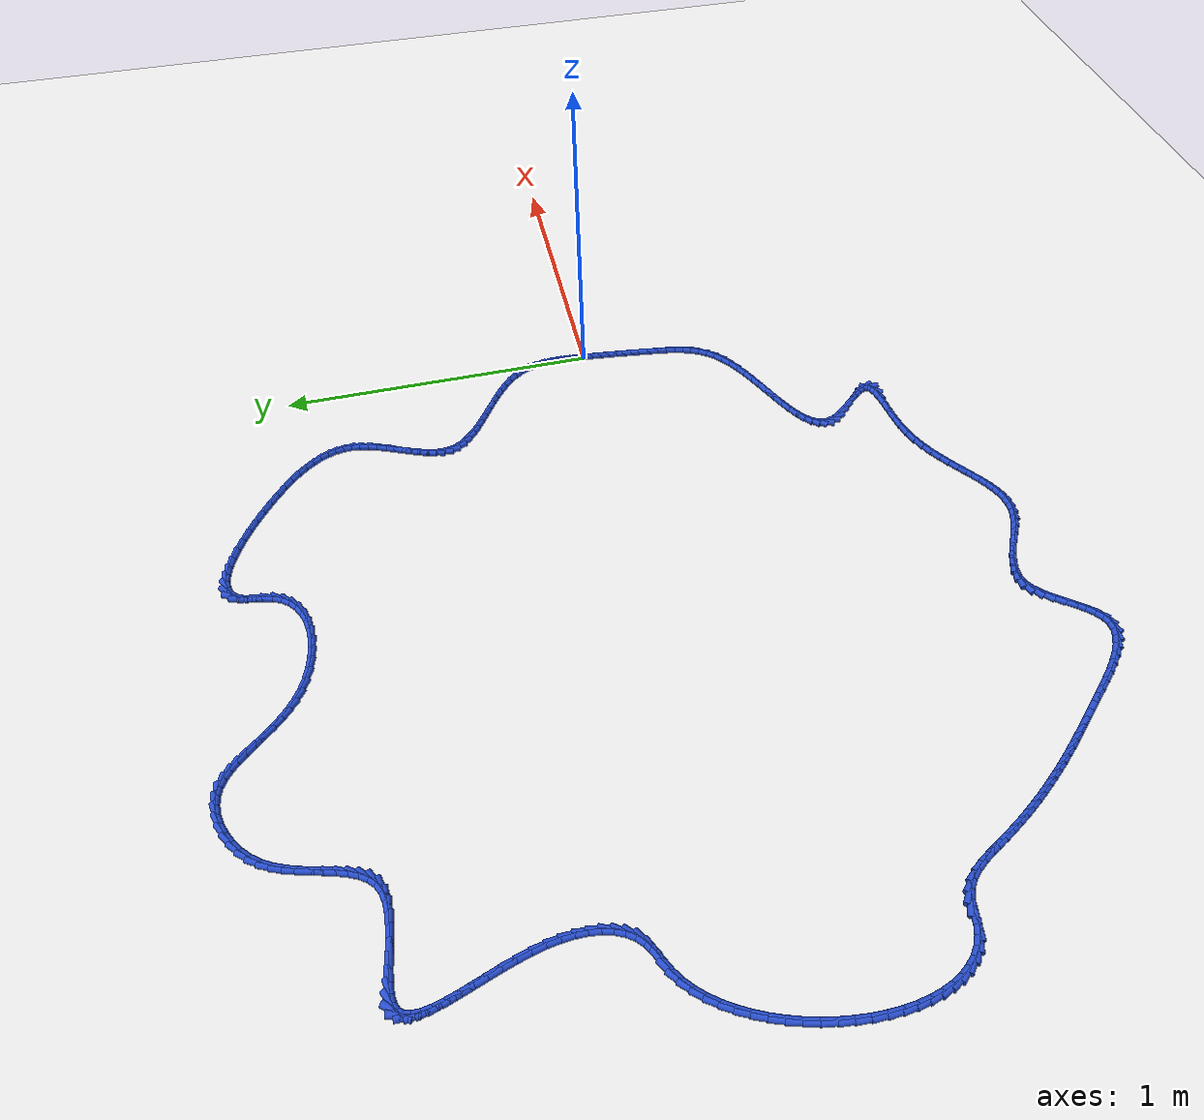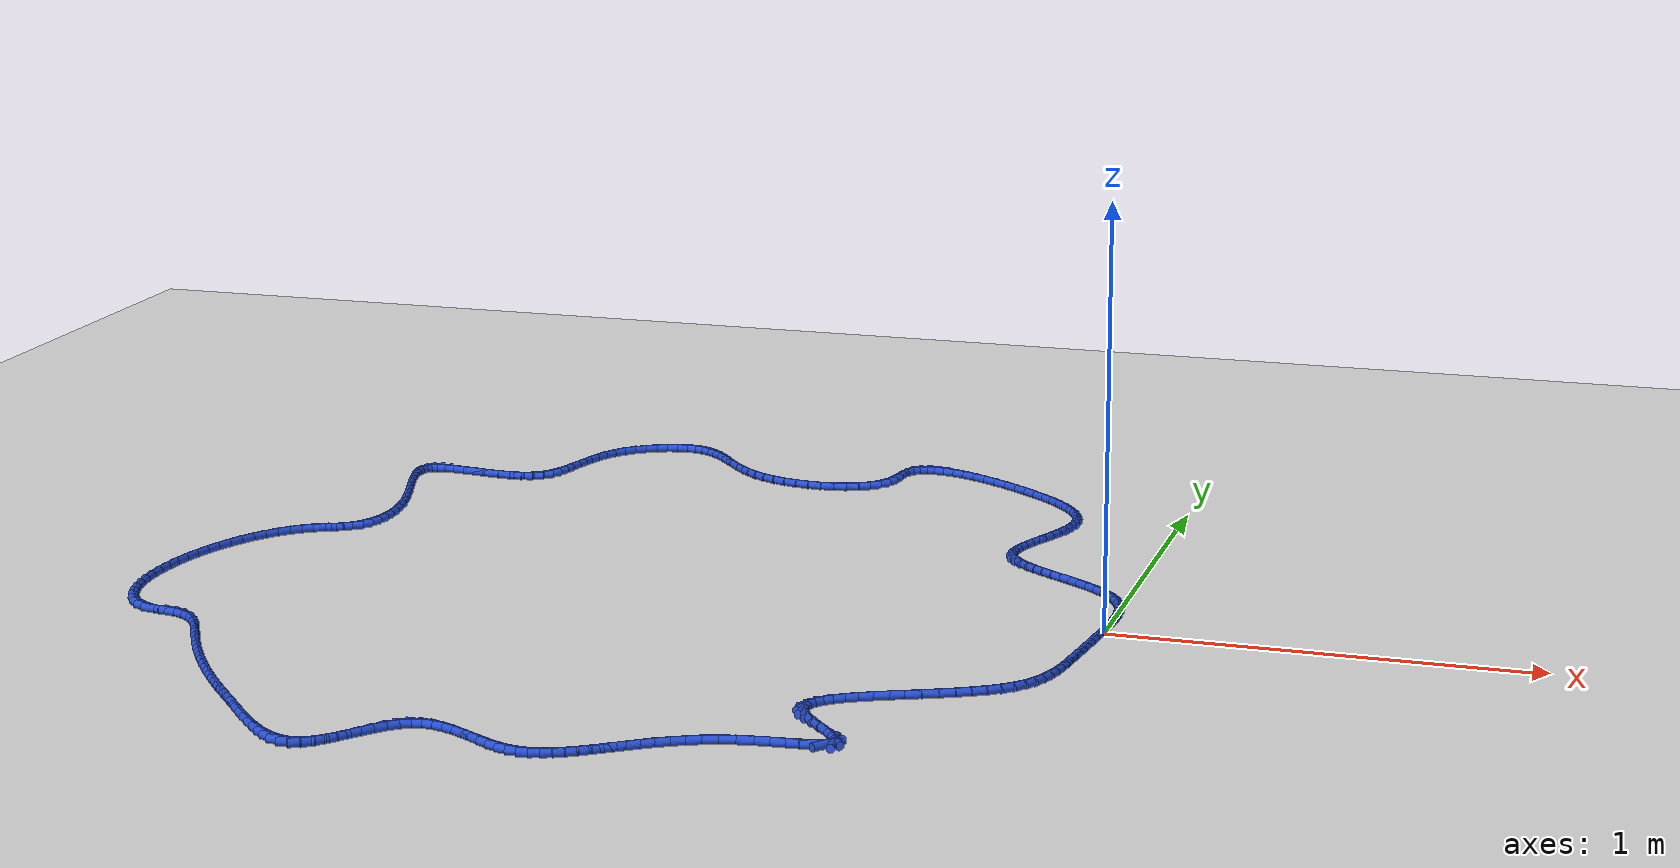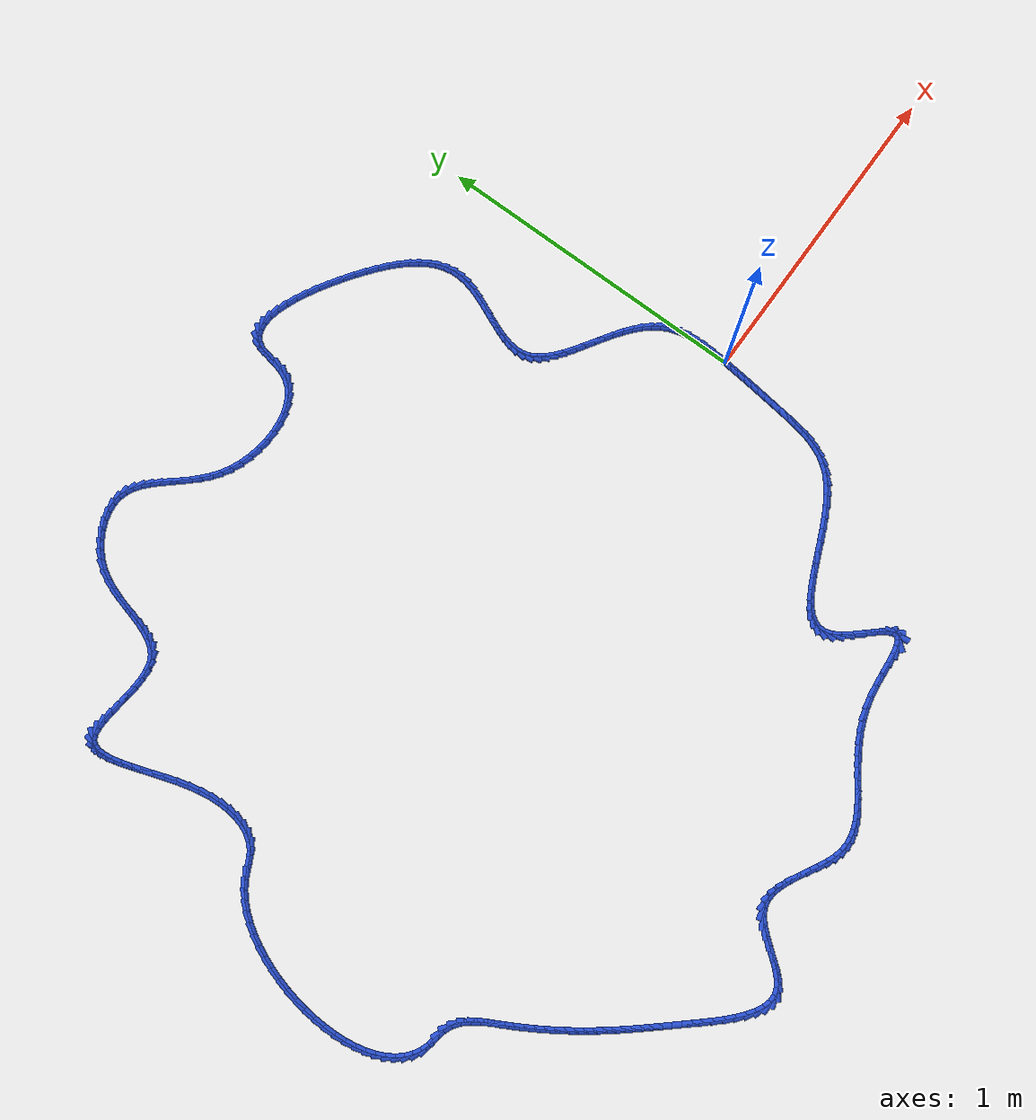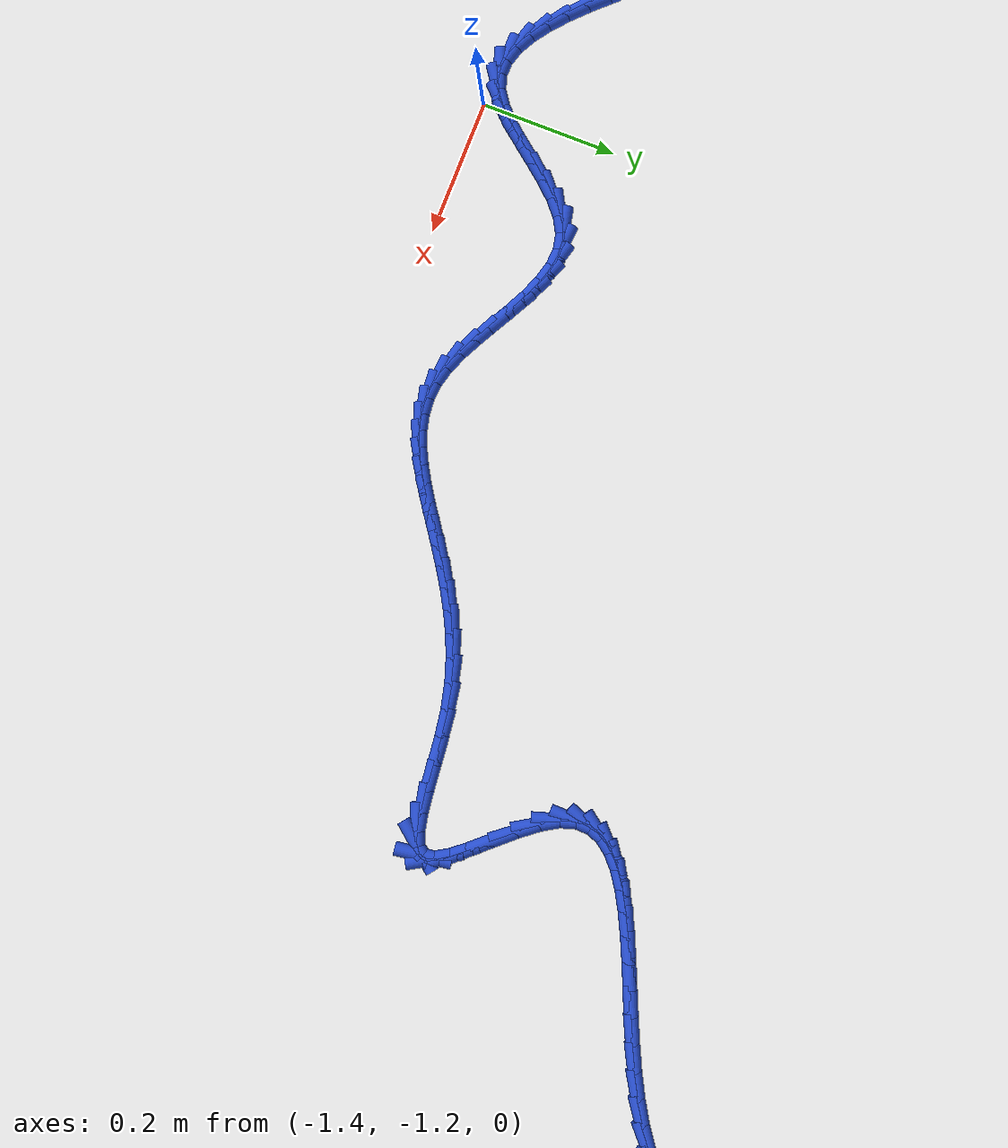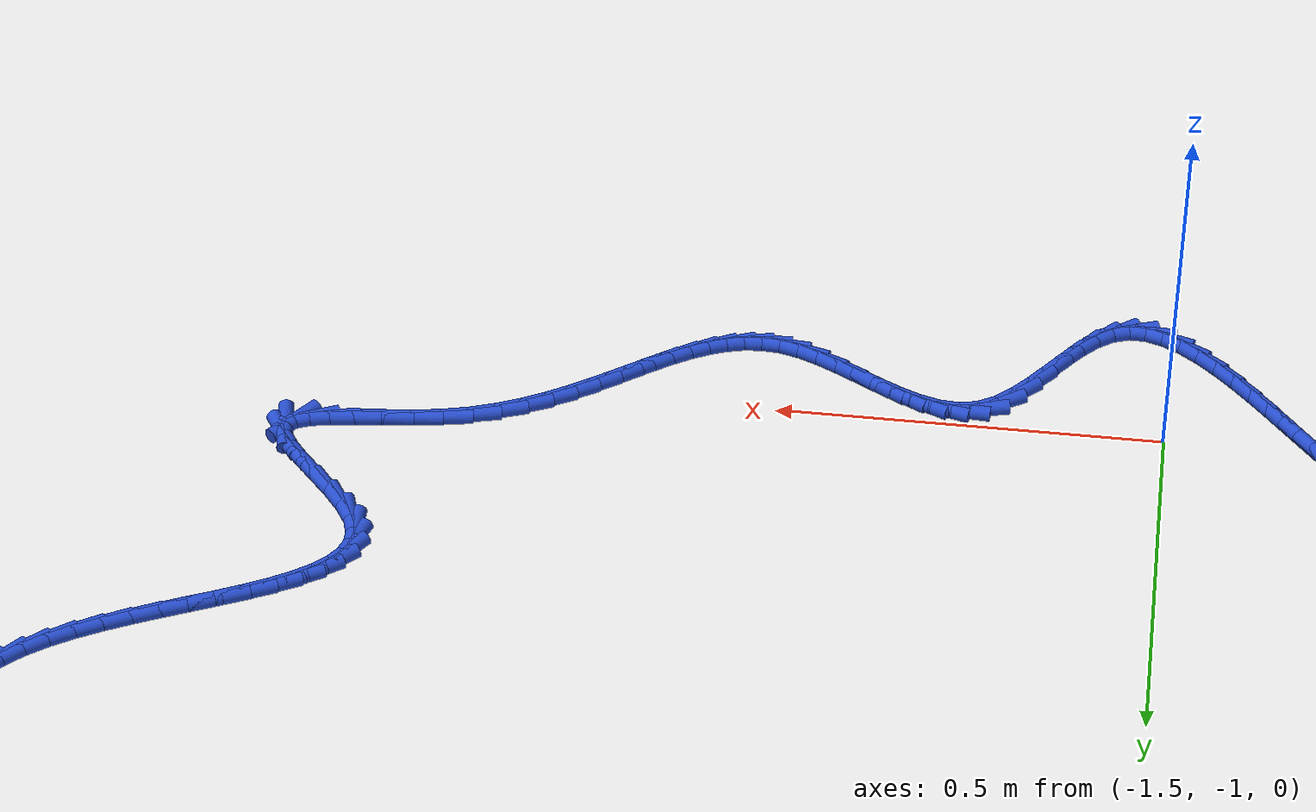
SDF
<sdf version="1.6">
 <world name="default">
  <light name="sun" type="directional">
   <pose>0 0 10 0 -0 0</pose>
   <diffuse>0.8 0.8 0.8 1</diffuse>
   <specular>0.2 0.2 0.2 1</specular>
   <attenuation>
    <range>1000</range>
    <constant>0.9</constant>
    <linear>0.01</linear>
    <quadratic>0.001</quadratic>
   </attenuation>
   <direction>-0.5 0.1 -0.9</direction>
  </light>
  <model name="ground_plane">
   <static>1</static>
   <link name="link">
    <collision name="collision">
     <geometry><plane><normal>0 0 1</normal><size>100 100</size></plane></geometry>
     <surface><friction><ode><mu>100</mu><mu2>50</mu2></ode></friction></surface>
    </collision>
    <visual name="visual">
     <cast_shadows>0</cast_shadows>
     <geometry><plane><normal>0 0 1</normal><size>100 100</size></plane></geometry>
     <material>
      <script><uri>file://media/materials/scripts/gazebo.material</uri><name>Gazebo/WhiteGlow</name></script>
     </material>
    </visual>
   </link>
  </model>
  <gravity>0 0 -9.8</gravity>
  <magnetic_field>6e-06 2.3e-05 -4.2e-05</magnetic_field>
  <atmosphere type="adiabatic"/>
  <physics name="default_physics" default="0" type="ode">
   <max_step_size>0.001</max_step_size>
   <real_time_factor>1</real_time_factor>
   <real_time_update_rate>1000</real_time_update_rate>
  </physics>
  <scene><ambient>0.4 0.4 0.4 1</ambient><background>0.7 0.7 0.7 1</background><shadows>1</shadows></scene>
  <spherical_coordinates>
   <surface_model>EARTH_WGS84</surface_model>
   <latitude_deg>0</latitude_deg>
   <longitude_deg>0</longitude_deg>
   <elevation>0</elevation>
   <heading_deg>0</heading_deg>
  </spherical_coordinates>
  <model name="line">
   <link name="link_0">
    <pose>-9.974659986866641e-18 9.71445146547012e-17 0.01 0 1.57 1.487251406768959</pose>
    <collision name="collision">
     <geometry><cylinder><radius>0.01</radius><length>0.08</length></cylinder></geometry>
    </collision>
    <visual name="visual">
     <material>
      <script><name>Gazebo/Blue</name><uri>file://media/materials/scripts/gazebo.material</uri></script>
     </material>
     <geometry><cylinder><radius>0.01</radius><length>0.08</length></cylinder></geometry>
    </visual>
   </link>
   <link name="link_1">
    <pose>0.0024495682638747515 0.02925212546453676 0.01 0 1.57 1.5105407258994081</pose>
    <collision name="collision">
     <geometry><cylinder><radius>0.01</radius><length>0.08</length></cylinder></geometry>
    </collision>
    <visual name="visual">
     <material>
      <script><name>Gazebo/Blue</name><uri>file://media/materials/scripts/gazebo.material</uri></script>
     </material>
     <geometry><cylinder><radius>0.01</radius><length>0.08</length></cylinder></geometry>
    </visual>
   </link>
   <link name="link_2">
    <pose>0.004228482738991206 0.05873919394650529 0.01 0 1.57 1.5495581520209312</pose>
    <collision name="collision">
     <geometry><cylinder><radius>0.01</radius><length>0.08</length></cylinder></geometry>
    </collision>
    <visual name="visual">
     <material>
      <script><name>Gazebo/Blue</name><uri>file://media/materials/scripts/gazebo.material</uri></script>
     </material>
     <geometry><cylinder><radius>0.01</radius><length>0.08</length></cylinder></geometry>
    </visual>
   </link>
   <link name="link_3">
    <pose>0.004853710855883276 0.08817364938218986 0.01 0 1.57 -1.536044362971187</pose>
    <collision name="collision">
     <geometry><cylinder><radius>0.01</radius><length>0.08</length></cylinder></geometry>
    </collision>
    <visual name="visual">
     <material>
      <script><name>Gazebo/Blue</name><uri>file://media/materials/scripts/gazebo.material</uri></script>
     </material>
     <geometry><cylinder><radius>0.01</radius><length>0.08</length></cylinder></geometry>
    </visual>
   </link>
   <link name="link_4">
    <pose>0.0038422200450848867 0.11726793570787472 0.01 0 1.57 -1.4612395565642085</pose>
    <collision name="collision">
     <geometry><cylinder><radius>0.01</radius><length>0.08</length></cylinder></geometry>
    </collision>
    <visual name="visual">
     <material>
      <script><name>Gazebo/Blue</name><uri>file://media/materials/scripts/gazebo.material</uri></script>
     </material>
     <geometry><cylinder><radius>0.01</radius><length>0.08</length></cylinder></geometry>
    </visual>
   </link>
   <link name="link_5">
    <pose>0.000710977737129961 0.1457344968598441 0.01 0 1.57 -1.3656035269785924</pose>
    <collision name="collision">
     <geometry><cylinder><radius>0.01</radius><length>0.08</length></cylinder></geometry>
    </collision>
    <visual name="visual">
     <material>
      <script><name>Gazebo/Blue</name><uri>file://media/materials/scripts/gazebo.material</uri></script>
     </material>
     <geometry><cylinder><radius>0.01</radius><length>0.08</length></cylinder></geometry>
    </visual>
   </link>
   <link name="link_6">
    <pose>-0.005023048637447583 0.17328577677438217 0.01 0 1.57 -1.2477814903358084</pose>
    <collision name="collision">
     <geometry><cylinder><radius>0.01</radius><length>0.08</length></cylinder></geometry>
    </collision>
    <visual name="visual">
     <material>
      <script><name>Gazebo/Blue</name><uri>file://media/materials/scripts/gazebo.material</uri></script>
     </material>
     <geometry><cylinder><radius>0.01</radius><length>0.08</length></cylinder></geometry>
    </visual>
   </link>
   <link name="link_7">
    <pose>-0.013842891648113805 0.19963421938777318 0.01 0 1.57 -1.1084515625861266</pose>
    <collision name="collision">
     <geometry><cylinder><radius>0.01</radius><length>0.08</length></cylinder></geometry>
    </collision>
    <visual name="visual">
     <material>
      <script><name>Gazebo/Blue</name><uri>file://media/materials/scripts/gazebo.material</uri></script>
     </material>
     <geometry><cylinder><radius>0.01</radius><length>0.08</length></cylinder></geometry>
    </visual>
   </link>
   <link name="link_8">
    <pose>-0.026231483053913266 0.22449231513812304 0.01 0 1.57 -0.9607501914604886</pose>
    <collision name="collision">
     <geometry><cylinder><radius>0.01</radius><length>0.08</length></cylinder></geometry>
    </collision>
    <visual name="visual">
     <material>
      <script><name>Gazebo/Blue</name><uri>file://media/materials/scripts/gazebo.material</uri></script>
     </material>
     <geometry><cylinder><radius>0.01</radius><length>0.08</length></cylinder></geometry>
    </visual>
   </link>
   <link name="link_9">
    <pose>-0.04243924915800756 0.24767980455804334 0.01 0 1.57 -0.8368820884955975</pose>
    <collision name="collision">
     <geometry><cylinder><radius>0.01</radius><length>0.08</length></cylinder></geometry>
    </collision>
    <visual name="visual">
     <material>
      <script><name>Gazebo/Blue</name><uri>file://media/materials/scripts/gazebo.material</uri></script>
     </material>
     <geometry><cylinder><radius>0.01</radius><length>0.08</length></cylinder></geometry>
    </visual>
   </link>
   <link name="link_10">
    <pose>-0.061987898365337336 0.2693525711027094 0.01 0 1.57 -0.7411289601158716</pose>
    <collision name="collision">
     <geometry><cylinder><radius>0.01</radius><length>0.08</length></cylinder></geometry>
    </collision>
    <visual name="visual">
     <material>
      <script><name>Gazebo/Blue</name><uri>file://media/materials/scripts/gazebo.material</uri></script>
     </material>
     <geometry><cylinder><radius>0.01</radius><length>0.08</length></cylinder></geometry>
    </visual>
   </link>
   <link name="link_11">
    <pose>-0.08425675304448016 0.2897321780445642 0.01 0 1.57 -0.6700518799153489</pose>
    <collision name="collision">
     <geometry><cylinder><radius>0.01</radius><length>0.08</length></cylinder></geometry>
    </collision>
    <visual name="visual">
     <material>
      <script><name>Gazebo/Blue</name><uri>file://media/materials/scripts/gazebo.material</uri></script>
     </material>
     <geometry><cylinder><radius>0.01</radius><length>0.08</length></cylinder></geometry>
    </visual>
   </link>
   <link name="link_12">
    <pose>-0.10862513556401354 0.30904018865605126 0.01 0 1.57 -0.6201385105414714</pose>
    <collision name="collision">
     <geometry><cylinder><radius>0.01</radius><length>0.08</length></cylinder></geometry>
    </collision>
    <visual name="visual">
     <material>
      <script><name>Gazebo/Blue</name><uri>file://media/materials/scripts/gazebo.material</uri></script>
     </material>
     <geometry><cylinder><radius>0.01</radius><length>0.08</length></cylinder></geometry>
    </visual>
   </link>
   <link name="link_13">
    <pose>-0.13447236829251505 0.3274981662096138 0.01 0 1.57 -0.5886738410782767</pose>
    <collision name="collision">
     <geometry><cylinder><radius>0.01</radius><length>0.08</length></cylinder></geometry>
    </collision>
    <visual name="visual">
     <material>
      <script><name>Gazebo/Blue</name><uri>file://media/materials/scripts/gazebo.material</uri></script>
     </material>
     <geometry><cylinder><radius>0.01</radius><length>0.08</length></cylinder></geometry>
    </visual>
   </link>
   <link name="link_14">
    <pose>-0.1611777735985621 0.3453276739776952 0.01 0 1.57 -0.5740159463636794</pose>
    <collision name="collision">
     <geometry><cylinder><radius>0.01</radius><length>0.08</length></cylinder></geometry>
    </collision>
    <visual name="visual">
     <material>
      <script><name>Gazebo/Blue</name><uri>file://media/materials/scripts/gazebo.material</uri></script>
     </material>
     <geometry><cylinder><radius>0.01</radius><length>0.08</length></cylinder></geometry>
    </visual>
   </link>
   <link name="link_15">
    <pose>-0.18812067385073244 0.36275027523273856 0.01 0 1.57 -0.5756719464370353</pose>
    <collision name="collision">
     <geometry><cylinder><radius>0.01</radius><length>0.08</length></cylinder></geometry>
    </collision>
    <visual name="visual">
     <material>
      <script><name>Gazebo/Blue</name><uri>file://media/materials/scripts/gazebo.material</uri></script>
     </material>
     <geometry><cylinder><radius>0.01</radius><length>0.08</length></cylinder></geometry>
    </visual>
   </link>
   <link name="link_16">
    <pose>-0.21468039141760334 0.37998753324718737 0.01 0 1.57 -0.5943750627849352</pose>
    <collision name="collision">
     <geometry><cylinder><radius>0.01</radius><length>0.08</length></cylinder></geometry>
    </collision>
    <visual name="visual">
     <material>
      <script><name>Gazebo/Blue</name><uri>file://media/materials/scripts/gazebo.material</uri></script>
     </material>
     <geometry><cylinder><radius>0.01</radius><length>0.08</length></cylinder></geometry>
    </visual>
   </link>
   <link name="link_17">
    <pose>-0.24023624866775264 0.39726101129348484 0.01 0 1.57 -0.6322494054699238</pose>
    <collision name="collision">
     <geometry><cylinder><radius>0.01</radius><length>0.08</length></cylinder></geometry>
    </collision>
    <visual name="visual">
     <material>
      <script><name>Gazebo/Blue</name><uri>file://media/materials/scripts/gazebo.material</uri></script>
     </material>
     <geometry><cylinder><radius>0.01</radius><length>0.08</length></cylinder></geometry>
    </visual>
   </link>
   <link name="link_18">
    <pose>-0.2641675679697576 0.4147922726440743 0.01 0 1.57 -0.6930719671084805</pose>
    <collision name="collision">
     <geometry><cylinder><radius>0.01</radius><length>0.08</length></cylinder></geometry>
    </collision>
    <visual name="visual">
     <material>
      <script><name>Gazebo/Blue</name><uri>file://media/materials/scripts/gazebo.material</uri></script>
     </material>
     <geometry><cylinder><radius>0.01</radius><length>0.08</length></cylinder></geometry>
    </visual>
   </link>
   <link name="link_19">
    <pose>-0.28585367169219594 0.43280288057139904 0.01 0 1.57 -0.7825021488508537</pose>
    <collision name="collision">
     <geometry><cylinder><radius>0.01</radius><length>0.08</length></cylinder></geometry>
    </collision>
    <visual name="visual">
     <material>
      <script><name>Gazebo/Blue</name><uri>file://media/materials/scripts/gazebo.material</uri></script>
     </material>
     <geometry><cylinder><radius>0.01</radius><length>0.08</length></cylinder></geometry>
    </visual>
   </link>
   <link name="link_20">
    <pose>-0.3046738822036452 0.45151439834790236 0.01 0 1.57 -0.9077646450076717</pose>
    <collision name="collision">
     <geometry><cylinder><radius>0.01</radius><length>0.08</length></cylinder></geometry>
    </collision>
    <visual name="visual">
     <material>
      <script><name>Gazebo/Blue</name><uri>file://media/materials/scripts/gazebo.material</uri></script>
     </material>
     <geometry><cylinder><radius>0.01</radius><length>0.08</length></cylinder></geometry>
    </visual>
   </link>
   <link name="link_21">
    <pose>-0.32000752187268283 0.47114838924602753 0.01 0 1.57 -1.075429963759417</pose>
    <collision name="collision">
     <geometry><cylinder><radius>0.01</radius><length>0.08</length></cylinder></geometry>
    </collision>
    <visual name="visual">
     <material>
      <script><name>Gazebo/Blue</name><uri>file://media/materials/scripts/gazebo.material</uri></script>
     </material>
     <geometry><cylinder><radius>0.01</radius><length>0.08</length></cylinder></geometry>
    </visual>
   </link>
   <link name="link_22">
    <pose>-0.33123391306788624 0.4919264165382179 0.01 0 1.57 -1.2853421165258418</pose>
    <collision name="collision">
     <geometry><cylinder><radius>0.01</radius><length>0.08</length></cylinder></geometry>
    </collision>
    <visual name="visual">
     <material>
      <script><name>Gazebo/Blue</name><uri>file://media/materials/scripts/gazebo.material</uri></script>
     </material>
     <geometry><cylinder><radius>0.01</radius><length>0.08</length></cylinder></geometry>
    </visual>
   </link>
   <link name="link_23">
    <pose>-0.33773237815783325 0.5140700434969168 0.01 0 1.57 -1.514319083122611</pose>
    <collision name="collision">
     <geometry><cylinder><radius>0.01</radius><length>0.08</length></cylinder></geometry>
    </collision>
    <visual name="visual">
     <material>
      <script><name>Gazebo/Blue</name><uri>file://media/materials/scripts/gazebo.material</uri></script>
     </material>
     <geometry><cylinder><radius>0.01</radius><length>0.08</length></cylinder></geometry>
    </visual>
   </link>
   <link name="link_24">
    <pose>-0.33907086867658515 0.5377444831598893 0.01 0 1.57 1.4423959399795072</pose>
    <collision name="collision">
     <geometry><cylinder><radius>0.01</radius><length>0.08</length></cylinder></geometry>
    </collision>
    <visual name="visual">
     <material>
      <script><name>Gazebo/Blue</name><uri>file://media/materials/scripts/gazebo.material</uri></script>
     </material>
     <geometry><cylinder><radius>0.01</radius><length>0.08</length></cylinder></geometry>
    </visual>
   </link>
   <link name="link_25">
    <pose>-0.3358345021069804 0.5628110849509536 0.01 0 1.57 1.3139983009104146</pose>
    <collision name="collision">
     <geometry><cylinder><radius>0.01</radius><length>0.08</length></cylinder></geometry>
    </collision>
    <visual name="visual">
     <material>
      <script><name>Gazebo/Blue</name><uri>file://media/materials/scripts/gazebo.material</uri></script>
     </material>
     <geometry><cylinder><radius>0.01</radius><length>0.08</length></cylinder></geometry>
    </visual>
   </link>
   <link name="link_26">
    <pose>-0.32894972497070313 0.589029231180877 0.01 0 1.57 1.2304699367790497</pose>
    <collision name="collision">
     <geometry><cylinder><radius>0.01</radius><length>0.08</length></cylinder></geometry>
    </collision>
    <visual name="visual">
     <material>
      <script><name>Gazebo/Blue</name><uri>file://media/materials/scripts/gazebo.material</uri></script>
     </material>
     <geometry><cylinder><radius>0.01</radius><length>0.08</length></cylinder></geometry>
    </visual>
   </link>
   <link name="link_27">
    <pose>-0.3193432340762747 0.6161582293908558 0.01 0 1.57 1.1815804407903943</pose>
    <collision name="collision">
     <geometry><cylinder><radius>0.01</radius><length>0.08</length></cylinder></geometry>
    </collision>
    <visual name="visual">
     <material>
      <script><name>Gazebo/Blue</name><uri>file://media/materials/scripts/gazebo.material</uri></script>
     </material>
     <geometry><cylinder><radius>0.01</radius><length>0.08</length></cylinder></geometry>
    </visual>
   </link>
   <link name="link_28">
    <pose>-0.3079417262322162 0.6439573871220857 0.01 0 1.57 1.1607728836388596</pose>
    <collision name="collision">
     <geometry><cylinder><radius>0.01</radius><length>0.08</length></cylinder></geometry>
    </collision>
    <visual name="visual">
     <material>
      <script><name>Gazebo/Blue</name><uri>file://media/materials/scripts/gazebo.material</uri></script>
     </material>
     <geometry><cylinder><radius>0.01</radius><length>0.08</length></cylinder></geometry>
    </visual>
   </link>
   <link name="link_29">
    <pose>-0.2956718982470489 0.6721860119157623 0.01 0 1.57 1.164936784153566</pose>
    <collision name="collision">
     <geometry><cylinder><radius>0.01</radius><length>0.08</length></cylinder></geometry>
    </collision>
    <visual name="visual">
     <material>
      <script><name>Gazebo/Blue</name><uri>file://media/materials/scripts/gazebo.material</uri></script>
     </material>
     <geometry><cylinder><radius>0.01</radius><length>0.08</length></cylinder></geometry>
    </visual>
   </link>
   <link name="link_30">
    <pose>-0.28346044692929423 0.7006034113130818 0.01 0 1.57 1.1939365933632693</pose>
    <collision name="collision">
     <geometry><cylinder><radius>0.01</radius><length>0.08</length></cylinder></geometry>
    </collision>
    <visual name="visual">
     <material>
      <script><name>Gazebo/Blue</name><uri>file://media/materials/scripts/gazebo.material</uri></script>
     </material>
     <geometry><cylinder><radius>0.01</radius><length>0.08</length></cylinder></geometry>
    </visual>
   </link>
   <link name="link_31">
    <pose>-0.2722340690874734 0.7289688928552399 0.01 0 1.57 1.2504254797631473</pose>
    <collision name="collision">
     <geometry><cylinder><radius>0.01</radius><length>0.08</length></cylinder></geometry>
    </collision>
    <visual name="visual">
     <material>
      <script><name>Gazebo/Blue</name><uri>file://media/materials/scripts/gazebo.material</uri></script>
     </material>
     <geometry><cylinder><radius>0.01</radius><length>0.08</length></cylinder></geometry>
    </visual>
   </link>
   <link name="link_32">
    <pose>-0.2629194615301076 0.7570417640834323 0.01 0 1.57 1.3398349631236368</pose>
    <collision name="collision">
     <geometry><cylinder><radius>0.01</radius><length>0.08</length></cylinder></geometry>
    </collision>
    <visual name="visual">
     <material>
      <script><name>Gazebo/Blue</name><uri>file://media/materials/scripts/gazebo.material</uri></script>
     </material>
     <geometry><cylinder><radius>0.01</radius><length>0.08</length></cylinder></geometry>
    </visual>
   </link>
   <link name="link_33">
    <pose>-0.2564433210657181 0.7845813325388549 0.01 0 1.57 1.467790540479625</pose>
    <collision name="collision">
     <geometry><cylinder><radius>0.01</radius><length>0.08</length></cylinder></geometry>
    </collision>
    <visual name="visual">
     <material>
      <script><name>Gazebo/Blue</name><uri>file://media/materials/scripts/gazebo.material</uri></script>
     </material>
     <geometry><cylinder><radius>0.01</radius><length>0.08</length></cylinder></geometry>
    </visual>
   </link>
   <link name="link_34">
    <pose>-0.2536748404327567 0.8113631515840094 0.01 0 1.57 -1.5261954079239068</pose>
    <collision name="collision">
     <geometry><cylinder><radius>0.01</radius><length>0.08</length></cylinder></geometry>
    </collision>
    <visual name="visual">
     <material>
      <script><name>Gazebo/Blue</name><uri>file://media/materials/scripts/gazebo.material</uri></script>
     </material>
     <geometry><cylinder><radius>0.01</radius><length>0.08</length></cylinder></geometry>
    </visual>
   </link>
   <link name="link_35">
    <pose>-0.25483447080682603 0.8373460544690847 0.01 0 1.57 -1.3792264050667045</pose>
    <collision name="collision">
     <geometry><cylinder><radius>0.01</radius><length>0.08</length></cylinder></geometry>
    </collision>
    <visual name="visual">
     <material>
      <script><name>Gazebo/Blue</name><uri>file://media/materials/scripts/gazebo.material</uri></script>
     </material>
     <geometry><cylinder><radius>0.01</radius><length>0.08</length></cylinder></geometry>
    </visual>
   </link>
   <link name="link_36">
    <pose>-0.2597333084637775 0.8626045237634224 0.01 0 1.57 -1.2403211299335417</pose>
    <collision name="collision">
     <geometry><cylinder><radius>0.01</radius><length>0.08</length></cylinder></geometry>
    </collision>
    <visual name="visual">
     <material>
      <script><name>Gazebo/Blue</name><uri>file://media/materials/scripts/gazebo.material</uri></script>
     </material>
     <geometry><cylinder><radius>0.01</radius><length>0.08</length></cylinder></geometry>
    </visual>
   </link>
   <link name="link_37">
    <pose>-0.2681760282653409 0.8872148561887592 0.01 0 1.57 -1.114764269633036</pose>
    <collision name="collision">
     <geometry><cylinder><radius>0.01</radius><length>0.08</length></cylinder></geometry>
    </collision>
    <visual name="visual">
     <material>
      <script><name>Gazebo/Blue</name><uri>file://media/materials/scripts/gazebo.material</uri></script>
     </material>
     <geometry><cylinder><radius>0.01</radius><length>0.08</length></cylinder></geometry>
    </visual>
   </link>
   <link name="link_38">
    <pose>-0.2799673050732459 0.9112533484668306 0.01 0 1.57 -1.0051976495566326</pose>
    <collision name="collision">
     <geometry><cylinder><radius>0.01</radius><length>0.08</length></cylinder></geometry>
    </collision>
    <visual name="visual">
     <material>
      <script><name>Gazebo/Blue</name><uri>file://media/materials/scripts/gazebo.material</uri></script>
     </material>
     <geometry><cylinder><radius>0.01</radius><length>0.08</length></cylinder></geometry>
    </visual>
   </link>
   <link name="link_39">
    <pose>-0.2949118137492225 0.9347962973193731 0.01 0 1.57 -0.911985034639637</pose>
    <collision name="collision">
     <geometry><cylinder><radius>0.01</radius><length>0.08</length></cylinder></geometry>
    </collision>
    <visual name="visual">
     <material>
      <script><name>Gazebo/Blue</name><uri>file://media/materials/scripts/gazebo.material</uri></script>
     </material>
     <geometry><cylinder><radius>0.01</radius><length>0.08</length></cylinder></geometry>
    </visual>
   </link>
   <link name="link_40">
    <pose>-0.31281422915499996 0.9579199994681215 0.01 0 1.57 -0.8340585048815566</pose>
    <collision name="collision">
     <geometry><cylinder><radius>0.01</radius><length>0.08</length></cylinder></geometry>
    </collision>
    <visual name="visual">
     <material>
      <script><name>Gazebo/Blue</name><uri>file://media/materials/scripts/gazebo.material</uri></script>
     </material>
     <geometry><cylinder><radius>0.01</radius><length>0.08</length></cylinder></geometry>
    </visual>
   </link>
   <link name="link_41">
    <pose>-0.3334792261523084 0.9807007516348122 0.01 0 1.57 -0.7697008340949969</pose>
    <collision name="collision">
     <geometry><cylinder><radius>0.01</radius><length>0.08</length></cylinder></geometry>
    </collision>
    <visual name="visual">
     <material>
      <script><name>Gazebo/Blue</name><uri>file://media/materials/scripts/gazebo.material</uri></script>
     </material>
     <geometry><cylinder><radius>0.01</radius><length>0.08</length></cylinder></geometry>
    </visual>
   </link>
   <link name="link_42">
    <pose>-0.35671147960287725 1.003214850541181 0.01 0 1.57 -0.7170594254745618</pose>
    <collision name="collision">
     <geometry><cylinder><radius>0.01</radius><length>0.08</length></cylinder></geometry>
    </collision>
    <visual name="visual">
     <material>
      <script><name>Gazebo/Blue</name><uri>file://media/materials/scripts/gazebo.material</uri></script>
     </material>
     <geometry><cylinder><radius>0.01</radius><length>0.08</length></cylinder></geometry>
    </visual>
   </link>
   <link name="link_43">
    <pose>-0.38231566436843645 1.0255385929089647 0.01 0 1.57 -0.6744127164814446</pose>
    <collision name="collision">
     <geometry><cylinder><radius>0.01</radius><length>0.08</length></cylinder></geometry>
    </collision>
    <visual name="visual">
     <material>
      <script><name>Gazebo/Blue</name><uri>file://media/materials/scripts/gazebo.material</uri></script>
     </material>
     <geometry><cylinder><radius>0.01</radius><length>0.08</length></cylinder></geometry>
    </visual>
   </link>
   <link name="link_44">
    <pose>-0.41009645531071587 1.0477482754598981 0.01 0 1.57 -0.6402232148361074</pose>
    <collision name="collision">
     <geometry><cylinder><radius>0.01</radius><length>0.08</length></cylinder></geometry>
    </collision>
    <visual name="visual">
     <material>
      <script><name>Gazebo/Blue</name><uri>file://media/materials/scripts/gazebo.material</uri></script>
     </material>
     <geometry><cylinder><radius>0.01</radius><length>0.08</length></cylinder></geometry>
    </visual>
   </link>
   <link name="link_45">
    <pose>-0.439856244601543 1.069916069690906 0.01 0 1.57 -0.6103311489327337</pose>
    <collision name="collision">
     <geometry><cylinder><radius>0.01</radius><length>0.08</length></cylinder></geometry>
    </collision>
    <visual name="visual">
     <material>
      <script><name>Gazebo/Blue</name><uri>file://media/materials/scripts/gazebo.material</uri></script>
     </material>
     <geometry><cylinder><radius>0.01</radius><length>0.08</length></cylinder></geometry>
    </visual>
   </link>
   <link name="link_46">
    <pose>-0.4712730286407604 1.0918893419142146 0.01 0 1.57 -0.5790112832817943</pose>
    <collision name="collision">
     <geometry><cylinder><radius>0.01</radius><length>0.08</length></cylinder></geometry>
    </collision>
    <visual name="visual">
     <material>
      <script><name>Gazebo/Blue</name><uri>file://media/materials/scripts/gazebo.material</uri></script>
     </material>
     <geometry><cylinder><radius>0.01</radius><length>0.08</length></cylinder></geometry>
    </visual>
   </link>
   <link name="link_47">
    <pose>-0.5038388881625324 1.1131794759171287 0.01 0 1.57 -0.5443049999427603</pose>
    <collision name="collision">
     <geometry><cylinder><radius>0.01</radius><length>0.08</length></cylinder></geometry>
    </collision>
    <visual name="visual">
     <material>
      <script><name>Gazebo/Blue</name><uri>file://media/materials/scripts/gazebo.material</uri></script>
     </material>
     <geometry><cylinder><radius>0.01</radius><length>0.08</length></cylinder></geometry>
    </visual>
   </link>
   <link name="link_48">
    <pose>-0.5370306910361629 1.133270363146657 0.01 0 1.57 -0.5043061697665209</pose>
    <collision name="collision">
     <geometry><cylinder><radius>0.01</radius><length>0.08</length></cylinder></geometry>
    </collision>
    <visual name="visual">
     <material>
      <script><name>Gazebo/Blue</name><uri>file://media/materials/scripts/gazebo.material</uri></script>
     </material>
     <geometry><cylinder><radius>0.01</radius><length>0.08</length></cylinder></geometry>
    </visual>
   </link>
   <link name="link_49">
    <pose>-0.5703253051309546 1.151645895049807 0.01 0 1.57 -0.4564901034539718</pose>
    <collision name="collision">
     <geometry><cylinder><radius>0.01</radius><length>0.08</length></cylinder></geometry>
    </collision>
    <visual name="visual">
     <material>
      <script><name>Gazebo/Blue</name><uri>file://media/materials/scripts/gazebo.material</uri></script>
     </material>
     <geometry><cylinder><radius>0.01</radius><length>0.08</length></cylinder></geometry>
    </visual>
   </link>
   <link name="link_50">
    <pose>-0.6031995983162115 1.1677899630735884 0.01 0 1.57 -0.3972430532414807</pose>
    <collision name="collision">
     <geometry><cylinder><radius>0.01</radius><length>0.08</length></cylinder></geometry>
    </collision>
    <visual name="visual">
     <material>
      <script><name>Gazebo/Blue</name><uri>file://media/materials/scripts/gazebo.material</uri></script>
     </material>
     <geometry><cylinder><radius>0.01</radius><length>0.08</length></cylinder></geometry>
    </visual>
   </link>
   <link name="link_51">
    <pose>-0.6351304384612365 1.1811864586650083 0.01 0 1.57 -0.32110233207687755</pose>
    <collision name="collision">
     <geometry><cylinder><radius>0.01</radius><length>0.08</length></cylinder></geometry>
    </collision>
    <visual name="visual">
     <material>
      <script><name>Gazebo/Blue</name><uri>file://media/materials/scripts/gazebo.material</uri></script>
     </material>
     <geometry><cylinder><radius>0.01</radius><length>0.08</length></cylinder></geometry>
    </visual>
   </link>
   <link name="link_52">
    <pose>-0.6655946934353335 1.1913192732710756 0.01 0 1.57 -0.21951716079136824</pose>
    <collision name="collision">
     <geometry><cylinder><radius>0.01</radius><length>0.08</length></cylinder></geometry>
    </collision>
    <visual name="visual">
     <material>
      <script><name>Gazebo/Blue</name><uri>file://media/materials/scripts/gazebo.material</uri></script>
     </material>
     <geometry><cylinder><radius>0.01</radius><length>0.08</length></cylinder></geometry>
    </visual>
   </link>
   <link name="link_53">
    <pose>-0.6940692311078055 1.197672298338799 0.01 0 1.57 -0.07907181824994931</pose>
    <collision name="collision">
     <geometry><cylinder><radius>0.01</radius><length>0.08</length></cylinder></geometry>
    </collision>
    <visual name="visual">
     <material>
      <script><name>Gazebo/Blue</name><uri>file://media/materials/scripts/gazebo.material</uri></script>
     </material>
     <geometry><cylinder><radius>0.01</radius><length>0.08</length></cylinder></geometry>
    </visual>
   </link>
   <link name="link_54">
    <pose>-0.7200309193479563 1.199729425315187 0.01 0 1.57 0.11959210192839471</pose>
    <collision name="collision">
     <geometry><cylinder><radius>0.01</radius><length>0.08</length></cylinder></geometry>
    </collision>
    <visual name="visual">
     <material>
      <script><name>Gazebo/Blue</name><uri>file://media/materials/scripts/gazebo.material</uri></script>
     </material>
     <geometry><cylinder><radius>0.01</radius><length>0.08</length></cylinder></geometry>
    </visual>
   </link>
   <link name="link_55">
    <pose>-0.742956626025089 1.196974545647247 0.01 0 1.57 0.3953884988400861</pose>
    <collision name="collision">
     <geometry><cylinder><radius>0.01</radius><length>0.08</length></cylinder></geometry>
    </collision>
    <visual name="visual">
     <material>
      <script><name>Gazebo/Blue</name><uri>file://media/materials/scripts/gazebo.material</uri></script>
     </material>
     <geometry><cylinder><radius>0.01</radius><length>0.08</length></cylinder></geometry>
    </visual>
   </link>
   <link name="link_56">
    <pose>-0.7623232190085071 1.1888915507819882 0.01 0 1.57 0.7389729424121195</pose>
    <collision name="collision">
     <geometry><cylinder><radius>0.01</radius><length>0.08</length></cylinder></geometry>
    </collision>
    <visual name="visual">
     <material>
      <script><name>Gazebo/Blue</name><uri>file://media/materials/scripts/gazebo.material</uri></script>
     </material>
     <geometry><cylinder><radius>0.01</radius><length>0.08</length></cylinder></geometry>
    </visual>
   </link>
   <link name="link_57">
    <pose>-0.777607566167514 1.1749643321664183 0.01 0 1.57 1.0856273546207393</pose>
    <collision name="collision">
     <geometry><cylinder><radius>0.01</radius><length>0.08</length></cylinder></geometry>
    </collision>
    <visual name="visual">
     <material>
      <script><name>Gazebo/Blue</name><uri>file://media/materials/scripts/gazebo.material</uri></script>
     </material>
     <geometry><cylinder><radius>0.01</radius><length>0.08</length></cylinder></geometry>
    </visual>
   </link>
   <link name="link_58">
    <pose>-0.78829732631115 1.1546877977082746 0.01 0 1.57 1.3179236141662545</pose>
    <collision name="collision">
     <geometry><cylinder><radius>0.01</radius><length>0.08</length></cylinder></geometry>
    </collision>
    <visual name="visual">
     <material>
      <script><name>Gazebo/Blue</name><uri>file://media/materials/scripts/gazebo.material</uri></script>
     </material>
     <geometry><cylinder><radius>0.01</radius><length>0.08</length></cylinder></geometry>
    </visual>
   </link>
   <link name="link_59">
    <pose>-0.7950100142362742 1.1287103242829677 0.01 0 1.57 1.3839884861339886</pose>
    <collision name="collision">
     <geometry><cylinder><radius>0.01</radius><length>0.08</length></cylinder></geometry>
    </collision>
    <visual name="visual">
     <material>
      <script><name>Gazebo/Blue</name><uri>file://media/materials/scripts/gazebo.material</uri></script>
     </material>
     <geometry><cylinder><radius>0.01</radius><length>0.08</length></cylinder></geometry>
    </visual>
   </link>
   <link name="link_60">
    <pose>-0.8004687503628161 1.0998298996637195 0.01 0 1.57 1.3267923486755313</pose>
    <collision name="collision">
     <geometry><cylinder><radius>0.01</radius><length>0.08</length></cylinder></geometry>
    </collision>
    <visual name="visual">
     <material>
      <script><name>Gazebo/Blue</name><uri>file://media/materials/scripts/gazebo.material</uri></script>
     </material>
     <geometry><cylinder><radius>0.01</radius><length>0.08</length></cylinder></geometry>
    </visual>
   </link>
   <link name="link_61">
    <pose>-0.8076266340803541 1.071079296948224 0.01 0 1.57 1.1463534179987565</pose>
    <collision name="collision">
     <geometry><cylinder><radius>0.01</radius><length>0.08</length></cylinder></geometry>
    </collision>
    <visual name="visual">
     <material>
      <script><name>Gazebo/Blue</name><uri>file://media/materials/scripts/gazebo.material</uri></script>
     </material>
     <geometry><cylinder><radius>0.01</radius><length>0.08</length></cylinder></geometry>
    </visual>
   </link>
   <link name="link_62">
    <pose>-0.8192592788898396 1.0453383524557573 0.01 0 1.57 0.9109110789206015</pose>
    <collision name="collision">
     <geometry><cylinder><radius>0.01</radius><length>0.08</length></cylinder></geometry>
    </collision>
    <visual name="visual">
     <material>
      <script><name>Gazebo/Blue</name><uri>file://media/materials/scripts/gazebo.material</uri></script>
     </material>
     <geometry><cylinder><radius>0.01</radius><length>0.08</length></cylinder></geometry>
    </visual>
   </link>
   <link name="link_63">
    <pose>-0.836056799253701 1.0236898610235108 0.01 0 1.57 0.6918155035580323</pose>
    <collision name="collision">
     <geometry><cylinder><radius>0.01</radius><length>0.08</length></cylinder></geometry>
    </collision>
    <visual name="visual">
     <material>
      <script><name>Gazebo/Blue</name><uri>file://media/materials/scripts/gazebo.material</uri></script>
     </material>
     <geometry><cylinder><radius>0.01</radius><length>0.08</length></cylinder></geometry>
    </visual>
   </link>
   <link name="link_64">
    <pose>-0.8573531970695129 1.006048076775687 0.01 0 1.57 0.5007708199092508</pose>
    <collision name="collision">
     <geometry><cylinder><radius>0.01</radius><length>0.08</length></cylinder></geometry>
    </collision>
    <visual name="visual">
     <material>
      <script><name>Gazebo/Blue</name><uri>file://media/materials/scripts/gazebo.material</uri></script>
     </material>
     <geometry><cylinder><radius>0.01</radius><length>0.08</length></cylinder></geometry>
    </visual>
   </link>
   <link name="link_65">
    <pose>-0.8824593899756058 0.992307362496008 0.01 0 1.57 0.33875205451915774</pose>
    <collision name="collision">
     <geometry><cylinder><radius>0.01</radius><length>0.08</length></cylinder></geometry>
    </collision>
    <visual name="visual">
     <material>
      <script><name>Gazebo/Blue</name><uri>file://media/materials/scripts/gazebo.material</uri></script>
     </material>
     <geometry><cylinder><radius>0.01</radius><length>0.08</length></cylinder></geometry>
    </visual>
   </link>
   <link name="link_66">
    <pose>-0.9106862956103109 0.9823620809681969 0.01 0 1.57 0.20127458190848088</pose>
    <collision name="collision">
     <geometry><cylinder><radius>0.01</radius><length>0.08</length></cylinder></geometry>
    </collision>
    <visual name="visual">
     <material>
      <script><name>Gazebo/Blue</name><uri>file://media/materials/scripts/gazebo.material</uri></script>
     </material>
     <geometry><cylinder><radius>0.01</radius><length>0.08</length></cylinder></geometry>
    </visual>
   </link>
   <link name="link_67">
    <pose>-0.9413448316119587 0.9761065949759763 0.01 0 1.57 0.08225958271098206</pose>
    <collision name="collision">
     <geometry><cylinder><radius>0.01</radius><length>0.08</length></cylinder></geometry>
    </collision>
    <visual name="visual">
     <material>
      <script><name>Gazebo/Blue</name><uri>file://media/materials/scripts/gazebo.material</uri></script>
     </material>
     <geometry><cylinder><radius>0.01</radius><length>0.08</length></cylinder></geometry>
    </visual>
   </link>
   <link name="link_68">
    <pose>-0.973745915618881 0.9734352673030692 0.01 0 1.57 -0.024123380938406897</pose>
    <collision name="collision">
     <geometry><cylinder><radius>0.01</radius><length>0.08</length></cylinder></geometry>
    </collision>
    <visual name="visual">
     <material>
      <script><name>Gazebo/Blue</name><uri>file://media/materials/scripts/gazebo.material</uri></script>
     </material>
     <geometry><cylinder><radius>0.01</radius><length>0.08</length></cylinder></geometry>
    </visual>
   </link>
   <link name="link_69">
    <pose>-1.0072004652694073 0.9742424607331976 0.01 0 1.57 -0.1229779624186971</pose>
    <collision name="collision">
     <geometry><cylinder><radius>0.01</radius><length>0.08</length></cylinder></geometry>
    </collision>
    <visual name="visual">
     <material>
      <script><name>Gazebo/Blue</name><uri>file://media/materials/scripts/gazebo.material</uri></script>
     </material>
     <geometry><cylinder><radius>0.01</radius><length>0.08</length></cylinder></geometry>
    </visual>
   </link>
   <link name="link_70">
    <pose>-1.0410193982018698 0.978422538050085 0.01 0 1.57 -0.21878732437438264</pose>
    <collision name="collision">
     <geometry><cylinder><radius>0.01</radius><length>0.08</length></cylinder></geometry>
    </collision>
    <visual name="visual">
     <material>
      <script><name>Gazebo/Blue</name><uri>file://media/materials/scripts/gazebo.material</uri></script>
     </material>
     <geometry><cylinder><radius>0.01</radius><length>0.08</length></cylinder></geometry>
    </visual>
   </link>
   <link name="link_71">
    <pose>-1.074513632054598 0.9858698620374533 0.01 0 1.57 -0.3157011110414314</pose>
    <collision name="collision">
     <geometry><cylinder><radius>0.01</radius><length>0.08</length></cylinder></geometry>
    </collision>
    <visual name="visual">
     <material>
      <script><name>Gazebo/Blue</name><uri>file://media/materials/scripts/gazebo.material</uri></script>
     </material>
     <geometry><cylinder><radius>0.01</radius><length>0.08</length></cylinder></geometry>
    </visual>
   </link>
   <link name="link_72">
    <pose>-1.1069940844659236 0.9964787954790258 0.01 0 1.57 -0.41784380704758606</pose>
    <collision name="collision">
     <geometry><cylinder><radius>0.01</radius><length>0.08</length></cylinder></geometry>
    </collision>
    <visual name="visual">
     <material>
      <script><name>Gazebo/Blue</name><uri>file://media/materials/scripts/gazebo.material</uri></script>
     </material>
     <geometry><cylinder><radius>0.01</radius><length>0.08</length></cylinder></geometry>
    </visual>
   </link>
   <link name="link_73">
    <pose>-1.1377716730741774 1.010143701158525 0.01 0 1.57 -0.5291703141802985</pose>
    <collision name="collision">
     <geometry><cylinder><radius>0.01</radius><length>0.08</length></cylinder></geometry>
    </collision>
    <visual name="visual">
     <material>
      <script><name>Gazebo/Blue</name><uri>file://media/materials/scripts/gazebo.material</uri></script>
     </material>
     <geometry><cylinder><radius>0.01</radius><length>0.08</length></cylinder></geometry>
    </visual>
   </link>
   <link name="link_74">
    <pose>-1.1661710005143981 1.0267517141214495 0.01 0 1.57 -0.6389277445847301</pose>
    <collision name="collision">
     <geometry><cylinder><radius>0.01</radius><length>0.08</length></cylinder></geometry>
    </collision>
    <visual name="visual">
     <material>
      <script><name>Gazebo/Blue</name><uri>file://media/materials/scripts/gazebo.material</uri></script>
     </material>
     <geometry><cylinder><radius>0.01</radius><length>0.08</length></cylinder></geometry>
    </visual>
   </link>
   <link name="link_75">
    <pose>-1.1919962044209704 1.0459367027506685 0.01 0 1.57 -0.7280658258280428</pose>
    <collision name="collision">
     <geometry><cylinder><radius>0.01</radius><length>0.08</length></cylinder></geometry>
    </collision>
    <visual name="visual">
     <material>
      <script><name>Gazebo/Blue</name><uri>file://media/materials/scripts/gazebo.material</uri></script>
     </material>
     <geometry><cylinder><radius>0.01</radius><length>0.08</length></cylinder></geometry>
    </visual>
   </link>
   <link name="link_76">
    <pose>-1.2156455946511369 1.067018723056404 0.01 0 1.57 -0.7937885537471916</pose>
    <collision name="collision">
     <geometry><cylinder><radius>0.01</radius><length>0.08</length></cylinder></geometry>
    </collision>
    <visual name="visual">
     <material>
      <script><name>Gazebo/Blue</name><uri>file://media/materials/scripts/gazebo.material</uri></script>
     </material>
     <geometry><cylinder><radius>0.01</radius><length>0.08</length></cylinder></geometry>
    </visual>
   </link>
   <link name="link_77">
    <pose>-1.2375544242406193 1.0892983194896944 0.01 0 1.57 -0.8354745881735959</pose>
    <collision name="collision">
     <geometry><cylinder><radius>0.01</radius><length>0.08</length></cylinder></geometry>
    </collision>
    <visual name="visual">
     <material>
      <script><name>Gazebo/Blue</name><uri>file://media/materials/scripts/gazebo.material</uri></script>
     </material>
     <geometry><cylinder><radius>0.01</radius><length>0.08</length></cylinder></geometry>
    </visual>
   </link>
   <link name="link_78">
    <pose>-1.2581579462251424 1.1120760365015798 0.01 0 1.57 -0.8524900523490971</pose>
    <collision name="collision">
     <geometry><cylinder><radius>0.01</radius><length>0.08</length></cylinder></geometry>
    </collision>
    <visual name="visual">
     <material>
      <script><name>Gazebo/Blue</name><uri>file://media/materials/scripts/gazebo.material</uri></script>
     </material>
     <geometry><cylinder><radius>0.01</radius><length>0.08</length></cylinder></geometry>
    </visual>
   </link>
   <link name="link_79">
    <pose>-1.2778914136404274 1.1346524185430966 0.01 0 1.57 -0.8433434416330472</pose>
    <collision name="collision">
     <geometry><cylinder><radius>0.01</radius><length>0.08</length></cylinder></geometry>
    </collision>
    <visual name="visual">
     <material>
      <script><name>Gazebo/Blue</name><uri>file://media/materials/scripts/gazebo.material</uri></script>
     </material>
     <geometry><cylinder><radius>0.01</radius><length>0.08</length></cylinder></geometry>
    </visual>
   </link>
   <link name="link_80">
    <pose>-1.297190079522197 1.1563280100652846 0.01 0 1.57 -0.8051096078013329</pose>
    <collision name="collision">
     <geometry><cylinder><radius>0.01</radius><length>0.08</length></cylinder></geometry>
    </collision>
    <visual name="visual">
     <material>
      <script><name>Gazebo/Blue</name><uri>file://media/materials/scripts/gazebo.material</uri></script>
     </material>
     <geometry><cylinder><radius>0.01</radius><length>0.08</length></cylinder></geometry>
    </visual>
   </link>
   <link name="link_81">
    <pose>-1.3164891969061745 1.176403355519182 0.01 0 1.57 -0.7332154081040344</pose>
    <collision name="collision">
     <geometry><cylinder><radius>0.01</radius><length>0.08</length></cylinder></geometry>
    </collision>
    <visual name="visual">
     <material>
      <script><name>Gazebo/Blue</name><uri>file://media/materials/scripts/gazebo.material</uri></script>
     </material>
     <geometry><cylinder><radius>0.01</radius><length>0.08</length></cylinder></geometry>
    </visual>
   </link>
   <link name="link_82">
    <pose>-1.3362240188280827 1.1941789993558274 0.01 0 1.57 -0.6221131544172135</pose>
    <collision name="collision">
     <geometry><cylinder><radius>0.01</radius><length>0.08</length></cylinder></geometry>
    </collision>
    <visual name="visual">
     <material>
      <script><name>Gazebo/Blue</name><uri>file://media/materials/scripts/gazebo.material</uri></script>
     </material>
     <geometry><cylinder><radius>0.01</radius><length>0.08</length></cylinder></geometry>
    </visual>
   </link>
   <link name="link_83">
    <pose>-1.356829798323644 1.208955486026259 0.01 0 1.57 -0.4680874627654028</pose>
    <collision name="collision">
     <geometry><cylinder><radius>0.01</radius><length>0.08</length></cylinder></geometry>
    </collision>
    <visual name="visual">
     <material>
      <script><name>Gazebo/Blue</name><uri>file://media/materials/scripts/gazebo.material</uri></script>
     </material>
     <geometry><cylinder><radius>0.01</radius><length>0.08</length></cylinder></geometry>
    </visual>
   </link>
   <link name="link_84">
    <pose>-1.3787417884285813 1.2200333599815159 0.01 0 1.57 -0.2752355873522919</pose>
    <collision name="collision">
     <geometry><cylinder><radius>0.01</radius><length>0.08</length></cylinder></geometry>
    </collision>
    <visual name="visual">
     <material>
      <script><name>Gazebo/Blue</name><uri>file://media/materials/scripts/gazebo.material</uri></script>
     </material>
     <geometry><cylinder><radius>0.01</radius><length>0.08</length></cylinder></geometry>
    </visual>
   </link>
   <link name="link_85">
    <pose>-1.4023952421786179 1.2267131656726367 0.01 0 1.57 -0.0679125623218019</pose>
    <collision name="collision">
     <geometry><cylinder><radius>0.01</radius><length>0.08</length></cylinder></geometry>
    </collision>
    <visual name="visual">
     <material>
      <script><name>Gazebo/Blue</name><uri>file://media/materials/scripts/gazebo.material</uri></script>
     </material>
     <geometry><cylinder><radius>0.01</radius><length>0.08</length></cylinder></geometry>
    </visual>
   </link>
   <link name="link_86">
    <pose>-1.428034095262341 1.228457047700716 0.01 0 1.57 0.11219825702227769</pose>
    <collision name="collision">
     <geometry><cylinder><radius>0.01</radius><length>0.08</length></cylinder></geometry>
    </collision>
    <visual name="visual">
     <material>
      <script><name>Gazebo/Blue</name><uri>file://media/materials/scripts/gazebo.material</uri></script>
     </material>
     <geometry><cylinder><radius>0.01</radius><length>0.08</length></cylinder></geometry>
    </visual>
   </link>
   <link name="link_87">
    <pose>-1.4550963424336887 1.2254079053288112 0.01 0 1.57 0.26498773636997586</pose>
    <collision name="collision">
     <geometry><cylinder><radius>0.01</radius><length>0.08</length></cylinder></geometry>
    </collision>
    <visual name="visual">
     <material>
      <script><name>Gazebo/Blue</name><uri>file://media/materials/scripts/gazebo.material</uri></script>
     </material>
     <geometry><cylinder><radius>0.01</radius><length>0.08</length></cylinder></geometry>
    </visual>
   </link>
   <link name="link_88">
    <pose>-1.4828077907036987 1.2178878665810215 0.01 0 1.57 0.40016728120694955</pose>
    <collision name="collision">
     <geometry><cylinder><radius>0.01</radius><length>0.08</length></cylinder></geometry>
    </collision>
    <visual name="visual">
     <material>
      <script><name>Gazebo/Blue</name><uri>file://media/materials/scripts/gazebo.material</uri></script>
     </material>
     <geometry><cylinder><radius>0.01</radius><length>0.08</length></cylinder></geometry>
    </visual>
   </link>
   <link name="link_89">
    <pose>-1.510394246047322 1.2062190603565983 0.01 0 1.57 0.5260555331266743</pose>
    <collision name="collision">
     <geometry><cylinder><radius>0.01</radius><length>0.08</length></cylinder></geometry>
    </collision>
    <visual name="visual">
     <material>
      <script><name>Gazebo/Blue</name><uri>file://media/materials/scripts/gazebo.material</uri></script>
     </material>
     <geometry><cylinder><radius>0.01</radius><length>0.08</length></cylinder></geometry>
    </visual>
   </link>
   <link name="link_90">
    <pose>-1.5370815144395094 1.1907236155547936 0.01 0 1.57 0.6496017822226671</pose>
    <collision name="collision">
     <geometry><cylinder><radius>0.01</radius><length>0.08</length></cylinder></geometry>
    </collision>
    <visual name="visual">
     <material>
      <script><name>Gazebo/Blue</name><uri>file://media/materials/scripts/gazebo.material</uri></script>
     </material>
     <geometry><cylinder><radius>0.01</radius><length>0.08</length></cylinder></geometry>
    </visual>
   </link>
   <link name="link_91">
    <pose>-1.5620954018552116 1.1717236610748585 0.01 0 1.57 0.7768176195879356</pose>
    <collision name="collision">
     <geometry><cylinder><radius>0.01</radius><length>0.08</length></cylinder></geometry>
    </collision>
    <visual name="visual">
     <material>
      <script><name>Gazebo/Blue</name><uri>file://media/materials/scripts/gazebo.material</uri></script>
     </material>
     <geometry><cylinder><radius>0.01</radius><length>0.08</length></cylinder></geometry>
    </visual>
   </link>
   <link name="link_92">
    <pose>-1.5846617142693786 1.1495413258160452 0.01 0 1.57 0.9130661441786372</pose>
    <collision name="collision">
     <geometry><cylinder><radius>0.01</radius><length>0.08</length></cylinder></geometry>
    </collision>
    <visual name="visual">
     <material>
      <script><name>Gazebo/Blue</name><uri>file://media/materials/scripts/gazebo.material</uri></script>
     </material>
     <geometry><cylinder><radius>0.01</radius><length>0.08</length></cylinder></geometry>
    </visual>
   </link>
   <link name="link_93">
    <pose>-1.604006432659625 1.1244987855724013 0.01 0 1.57 1.0522306613063315</pose>
    <collision name="collision">
     <geometry><cylinder><radius>0.01</radius><length>0.08</length></cylinder></geometry>
    </collision>
    <visual name="visual">
     <material>
      <script><name>Gazebo/Blue</name><uri>file://media/materials/scripts/gazebo.material</uri></script>
     </material>
     <geometry><cylinder><radius>0.01</radius><length>0.08</length></cylinder></geometry>
    </visual>
   </link>
   <link name="link_94">
    <pose>-1.619693802096249 1.0970088594764928 0.01 0 1.57 1.1628965667362776</pose>
    <collision name="collision">
     <geometry><cylinder><radius>0.01</radius><length>0.08</length></cylinder></geometry>
    </collision>
    <visual name="visual">
     <material>
      <script><name>Gazebo/Blue</name><uri>file://media/materials/scripts/gazebo.material</uri></script>
     </material>
     <geometry><cylinder><radius>0.01</radius><length>0.08</length></cylinder></geometry>
    </visual>
   </link>
   <link name="link_95">
    <pose>-1.6323315766809896 1.0677639917952988 0.01 0 1.57 1.2397936708424733</pose>
    <collision name="collision">
     <geometry><cylinder><radius>0.01</radius><length>0.08</length></cylinder></geometry>
    </collision>
    <visual name="visual">
     <material>
      <script><name>Gazebo/Blue</name><uri>file://media/materials/scripts/gazebo.material</uri></script>
     </material>
     <geometry><cylinder><radius>0.01</radius><length>0.08</length></cylinder></geometry>
    </visual>
   </link>
   <link name="link_96">
    <pose>-1.6427280965590259 1.0375103770726701 0.01 0 1.57 1.2850989451143071</pose>
    <collision name="collision">
     <geometry><cylinder><radius>0.01</radius><length>0.08</length></cylinder></geometry>
    </collision>
    <visual name="visual">
     <material>
      <script><name>Gazebo/Blue</name><uri>file://media/materials/scripts/gazebo.material</uri></script>
     </material>
     <geometry><cylinder><radius>0.01</radius><length>0.08</length></cylinder></geometry>
    </visual>
   </link>
   <link name="link_97">
    <pose>-1.651691701875538 1.0069942098524587 0.01 0 1.57 1.2999526392026173</pose>
    <collision name="collision">
     <geometry><cylinder><radius>0.01</radius><length>0.08</length></cylinder></geometry>
    </collision>
    <visual name="visual">
     <material>
      <script><name>Gazebo/Blue</name><uri>file://media/materials/scripts/gazebo.material</uri></script>
     </material>
     <geometry><cylinder><radius>0.01</radius><length>0.08</length></cylinder></geometry>
    </visual>
   </link>
   <link name="link_98">
    <pose>-1.6600307327757047 0.9769616846785142 0.01 0 1.57 1.2831026435063142</pose>
    <collision name="collision">
     <geometry><cylinder><radius>0.01</radius><length>0.08</length></cylinder></geometry>
    </collision>
    <visual name="visual">
     <material>
      <script><name>Gazebo/Blue</name><uri>file://media/materials/scripts/gazebo.material</uri></script>
     </material>
     <geometry><cylinder><radius>0.01</radius><length>0.08</length></cylinder></geometry>
    </visual>
   </link>
   <link name="link_99">
    <pose>-1.6685535294047065 0.9481589960946886 0.01 0 1.57 1.2299575588295677</pose>
    <collision name="collision">
     <geometry><cylinder><radius>0.01</radius><length>0.08</length></cylinder></geometry>
    </collision>
    <visual name="visual">
     <material>
      <script><name>Gazebo/Blue</name><uri>file://media/materials/scripts/gazebo.material</uri></script>
     </material>
     <geometry><cylinder><radius>0.01</radius><length>0.08</length></cylinder></geometry>
    </visual>
   </link>
   <link name="link_100">
    <pose>-1.678068431907722 0.921332338644832 0.01 0 1.57 1.1319022367469485</pose>
    <collision name="collision">
     <geometry><cylinder><radius>0.01</radius><length>0.08</length></cylinder></geometry>
    </collision>
    <visual name="visual">
     <material>
      <script><name>Gazebo/Blue</name><uri>file://media/materials/scripts/gazebo.material</uri></script>
     </material>
     <geometry><cylinder><radius>0.01</radius><length>0.08</length></cylinder></geometry>
    </visual>
   </link>
   <link name="link_101">
    <pose>-1.689383780429931 0.897227906872796 0.01 0 1.57 0.9772188972702817</pose>
    <collision name="collision">
     <geometry><cylinder><radius>0.01</radius><length>0.08</length></cylinder></geometry>
    </collision>
    <visual name="visual">
     <material>
      <script><name>Gazebo/Blue</name><uri>file://media/materials/scripts/gazebo.material</uri></script>
     </material>
     <geometry><cylinder><radius>0.01</radius><length>0.08</length></cylinder></geometry>
    </visual>
   </link>
   <link name="link_102">
    <pose>-1.7033079151165127 0.8765918953224315 0.01 0 1.57 0.7581598838678478</pose>
    <collision name="collision">
     <geometry><cylinder><radius>0.01</radius><length>0.08</length></cylinder></geometry>
    </collision>
    <visual name="visual">
     <material>
      <script><name>Gazebo/Blue</name><uri>file://media/materials/scripts/gazebo.material</uri></script>
     </material>
     <geometry><cylinder><radius>0.01</radius><length>0.08</length></cylinder></geometry>
    </visual>
   </link>
   <link name="link_103">
    <pose>-1.720649176112647 0.8601704985375895 0.01 0 1.57 0.48870775665935795</pose>
    <collision name="collision">
     <geometry><cylinder><radius>0.01</radius><length>0.08</length></cylinder></geometry>
    </collision>
    <visual name="visual">
     <material>
      <script><name>Gazebo/Blue</name><uri>file://media/materials/scripts/gazebo.material</uri></script>
     </material>
     <geometry><cylinder><radius>0.01</radius><length>0.08</length></cylinder></geometry>
    </visual>
   </link>
   <link name="link_104">
    <pose>-1.7422111058959737 0.8487053865791615 0.01 0 1.57 0.23930846050962265</pose>
    <collision name="collision">
     <geometry><cylinder><radius>0.01</radius><length>0.08</length></cylinder></geometry>
    </collision>
    <visual name="visual">
     <material>
      <script><name>Gazebo/Blue</name><uri>file://media/materials/scripts/gazebo.material</uri></script>
     </material>
     <geometry><cylinder><radius>0.01</radius><length>0.08</length></cylinder></geometry>
    </visual>
   </link>
   <link name="link_105">
    <pose>-1.7681911755950415 0.842366668542573 0.01 0 1.57 0.07351138348656047</pose>
    <collision name="collision">
     <geometry><cylinder><radius>0.01</radius><length>0.08</length></cylinder></geometry>
    </collision>
    <visual name="visual">
     <material>
      <script><name>Gazebo/Blue</name><uri>file://media/materials/scripts/gazebo.material</uri></script>
     </material>
     <geometry><cylinder><radius>0.01</radius><length>0.08</length></cylinder></geometry>
    </visual>
   </link>
   <link name="link_106">
    <pose>-1.7975957749724496 0.8402011936686257 0.01 0 1.57 -0.029133597090017935</pose>
    <collision name="collision">
     <geometry><cylinder><radius>0.01</radius><length>0.08</length></cylinder></geometry>
    </collision>
    <visual name="visual">
     <material>
      <script><name>Gazebo/Blue</name><uri>file://media/materials/scripts/gazebo.material</uri></script>
     </material>
     <geometry><cylinder><radius>0.01</radius><length>0.08</length></cylinder></geometry>
    </visual>
   </link>
   <link name="link_107">
    <pose>-1.8292924717186454 0.8411248938107417 0.01 0 1.57 -0.08890474475430889</pose>
    <collision name="collision">
     <geometry><cylinder><radius>0.01</radius><length>0.08</length></cylinder></geometry>
    </collision>
    <visual name="visual">
     <material>
      <script><name>Gazebo/Blue</name><uri>file://media/materials/scripts/gazebo.material</uri></script>
     </material>
     <geometry><cylinder><radius>0.01</radius><length>0.08</length></cylinder></geometry>
    </visual>
   </link>
   <link name="link_108">
    <pose>-1.862148833524075 0.8440537008223449 0.01 0 1.57 -0.11654442508154653</pose>
    <collision name="collision">
     <geometry><cylinder><radius>0.01</radius><length>0.08</length></cylinder></geometry>
    </collision>
    <visual name="visual">
     <material>
      <script><name>Gazebo/Blue</name><uri>file://media/materials/scripts/gazebo.material</uri></script>
     </material>
     <geometry><cylinder><radius>0.01</radius><length>0.08</length></cylinder></geometry>
    </visual>
   </link>
   <link name="link_109">
    <pose>-1.8950324280791855 0.8479035465568575 0.01 0 1.57 -0.11550008544488422</pose>
    <collision name="collision">
     <geometry><cylinder><radius>0.01</radius><length>0.08</length></cylinder></geometry>
    </collision>
    <visual name="visual">
     <material>
      <script><name>Gazebo/Blue</name><uri>file://media/materials/scripts/gazebo.material</uri></script>
     </material>
     <geometry><cylinder><radius>0.01</radius><length>0.08</length></cylinder></geometry>
    </visual>
   </link>
   <link name="link_110">
    <pose>-1.9268108230744228 0.8515903628677033 0.01 0 1.57 -0.0824012015688071</pose>
    <collision name="collision">
     <geometry><cylinder><radius>0.01</radius><length>0.08</length></cylinder></geometry>
    </collision>
    <visual name="visual">
     <material>
      <script><name>Gazebo/Blue</name><uri>file://media/materials/scripts/gazebo.material</uri></script>
     </material>
     <geometry><cylinder><radius>0.01</radius><length>0.08</length></cylinder></geometry>
    </visual>
   </link>
   <link name="link_111">
    <pose>-1.9563515862002336 0.8540300816083045 0.01 0 1.57 -0.004147860225591334</pose>
    <collision name="collision">
     <geometry><cylinder><radius>0.01</radius><length>0.08</length></cylinder></geometry>
    </collision>
    <visual name="visual">
     <material>
      <script><name>Gazebo/Blue</name><uri>file://media/materials/scripts/gazebo.material</uri></script>
     </material>
     <geometry><cylinder><radius>0.01</radius><length>0.08</length></cylinder></geometry>
    </visual>
   </link>
   <link name="link_112">
    <pose>-1.9825222851470647 0.8541386346320851 0.01 0 1.57 0.15143686277617685</pose>
    <collision name="collision">
     <geometry><cylinder><radius>0.01</radius><length>0.08</length></cylinder></geometry>
    </collision>
    <visual name="visual">
     <material>
      <script><name>Gazebo/Blue</name><uri>file://media/materials/scripts/gazebo.material</uri></script>
     </material>
     <geometry><cylinder><radius>0.01</radius><length>0.08</length></cylinder></geometry>
    </visual>
   </link>
   <link name="link_113">
    <pose>-2.0041904876053627 0.8508319537924668 0.01 0 1.57 0.45148331574570477</pose>
    <collision name="collision">
     <geometry><cylinder><radius>0.01</radius><length>0.08</length></cylinder></geometry>
    </collision>
    <visual name="visual">
     <material>
      <script><name>Gazebo/Blue</name><uri>file://media/materials/scripts/gazebo.material</uri></script>
     </material>
     <geometry><cylinder><radius>0.01</radius><length>0.08</length></cylinder></geometry>
    </visual>
   </link>
   <link name="link_114">
    <pose>-2.0202477103624323 0.8430460342551588 0.01 0 1.57 0.8953995065718137</pose>
    <collision name="collision">
     <geometry><cylinder><radius>0.01</radius><length>0.08</length></cylinder></geometry>
    </collision>
    <visual name="visual">
     <material>
      <script><name>Gazebo/Blue</name><uri>file://media/materials/scripts/gazebo.material</uri></script>
     </material>
     <geometry><cylinder><radius>0.01</radius><length>0.08</length></cylinder></geometry>
    </visual>
   </link>
   <link name="link_115">
    <pose>-2.0303872866230743 0.8303885914296413 0.01 0 1.57 1.2924898773404387</pose>
    <collision name="collision">
     <geometry><cylinder><radius>0.01</radius><length>0.08</length></cylinder></geometry>
    </collision>
    <visual name="visual">
     <material>
      <script><name>Gazebo/Blue</name><uri>file://media/materials/scripts/gazebo.material</uri></script>
     </material>
     <geometry><cylinder><radius>0.01</radius><length>0.08</length></cylinder></geometry>
    </visual>
   </link>
   <link name="link_116">
    <pose>-2.035275005782029 0.8132820141278225 0.01 0 1.57 1.5537176633979721</pose>
    <collision name="collision">
     <geometry><cylinder><radius>0.01</radius><length>0.08</length></cylinder></geometry>
    </collision>
    <visual name="visual">
     <material>
      <script><name>Gazebo/Blue</name><uri>file://media/materials/scripts/gazebo.material</uri></script>
     </material>
     <geometry><cylinder><radius>0.01</radius><length>0.08</length></cylinder></geometry>
    </visual>
   </link>
   <link name="link_117">
    <pose>-2.035635133056376 0.7921976791752984 0.01 0 1.57 -1.4316804758875932</pose>
    <collision name="collision">
     <geometry><cylinder><radius>0.01</radius><length>0.08</length></cylinder></geometry>
    </collision>
    <visual name="visual">
     <material>
      <script><name>Gazebo/Blue</name><uri>file://media/materials/scripts/gazebo.material</uri></script>
     </material>
     <geometry><cylinder><radius>0.01</radius><length>0.08</length></cylinder></geometry>
    </visual>
   </link>
   <link name="link_118">
    <pose>-2.032191933663193 0.7676069633976659 0.01 0 1.57 -1.3389480738570347</pose>
    <collision name="collision">
     <geometry><cylinder><radius>0.01</radius><length>0.08</length></cylinder></geometry>
    </collision>
    <visual name="visual">
     <material>
      <script><name>Gazebo/Blue</name><uri>file://media/materials/scripts/gazebo.material</uri></script>
     </material>
     <geometry><cylinder><radius>0.01</radius><length>0.08</length></cylinder></geometry>
    </visual>
   </link>
   <link name="link_119">
    <pose>-2.0256696728195602 0.7399812436205213 0.01 0 1.57 -1.2848108179512254</pose>
    <collision name="collision">
     <geometry><cylinder><radius>0.01</radius><length>0.08</length></cylinder></geometry>
    </collision>
    <visual name="visual">
     <material>
      <script><name>Gazebo/Blue</name><uri>file://media/materials/scripts/gazebo.material</uri></script>
     </material>
     <geometry><cylinder><radius>0.01</radius><length>0.08</length></cylinder></geometry>
    </visual>
   </link>
   <link name="link_120">
    <pose>-2.016792615742556 0.7097918966694611 0.01 0 1.57 -1.2561142731755144</pose>
    <collision name="collision">
     <geometry><cylinder><radius>0.01</radius><length>0.08</length></cylinder></geometry>
    </collision>
    <visual name="visual">
     <material>
      <script><name>Gazebo/Blue</name><uri>file://media/materials/scripts/gazebo.material</uri></script>
     </material>
     <geometry><cylinder><radius>0.01</radius><length>0.08</length></cylinder></geometry>
    </visual>
   </link>
   <link name="link_121">
    <pose>-2.006285027649259 0.6775102993700812 0.01 0 1.57 -1.2460481942176413</pose>
    <collision name="collision">
     <geometry><cylinder><radius>0.01</radius><length>0.08</length></cylinder></geometry>
    </collision>
    <visual name="visual">
     <material>
      <script><name>Gazebo/Blue</name><uri>file://media/materials/scripts/gazebo.material</uri></script>
     </material>
     <geometry><cylinder><radius>0.01</radius><length>0.08</length></cylinder></geometry>
    </visual>
   </link>
   <link name="link_122">
    <pose>-1.9948711737567473 0.643607828547978 0.01 0 1.57 -1.251310437616102</pose>
    <collision name="collision">
     <geometry><cylinder><radius>0.01</radius><length>0.08</length></cylinder></geometry>
    </collision>
    <visual name="visual">
     <material>
      <script><name>Gazebo/Blue</name><uri>file://media/materials/scripts/gazebo.material</uri></script>
     </material>
     <geometry><cylinder><radius>0.01</radius><length>0.08</length></cylinder></geometry>
    </visual>
   </link>
   <link name="link_123">
    <pose>-1.9832753192821013 0.6085558610287491 0.01 0 1.57 -1.2707713300149894</pose>
    <collision name="collision">
     <geometry><cylinder><radius>0.01</radius><length>0.08</length></cylinder></geometry>
    </collision>
    <visual name="visual">
     <material>
      <script><name>Gazebo/Blue</name><uri>file://media/materials/scripts/gazebo.material</uri></script>
     </material>
     <geometry><cylinder><radius>0.01</radius><length>0.08</length></cylinder></geometry>
    </visual>
   </link>
   <link name="link_124">
    <pose>-1.9722217294423987 0.5728257736379898 0.01 0 1.57 -1.3049041635913308</pose>
    <collision name="collision">
     <geometry><cylinder><radius>0.01</radius><length>0.08</length></cylinder></geometry>
    </collision>
    <visual name="visual">
     <material>
      <script><name>Gazebo/Blue</name><uri>file://media/materials/scripts/gazebo.material</uri></script>
     </material>
     <geometry><cylinder><radius>0.01</radius><length>0.08</length></cylinder></geometry>
    </visual>
   </link>
   <link name="link_125">
    <pose>-1.9624346694547188 0.5368889432012969 0.01 0 1.57 -1.3556266566789654</pose>
    <collision name="collision">
     <geometry><cylinder><radius>0.01</radius><length>0.08</length></cylinder></geometry>
    </collision>
    <visual name="visual">
     <material>
      <script><name>Gazebo/Blue</name><uri>file://media/materials/scripts/gazebo.material</uri></script>
     </material>
     <geometry><cylinder><radius>0.01</radius><length>0.08</length></cylinder></geometry>
    </visual>
   </link>
   <link name="link_126">
    <pose>-1.9546384045361402 0.5012167465442661 0.01 0 1.57 -1.424356072851804</pose>
    <collision name="collision">
     <geometry><cylinder><radius>0.01</radius><length>0.08</length></cylinder></geometry>
    </collision>
    <visual name="visual">
     <material>
      <script><name>Gazebo/Blue</name><uri>file://media/materials/scripts/gazebo.material</uri></script>
     </material>
     <geometry><cylinder><radius>0.01</radius><length>0.08</length></cylinder></geometry>
    </visual>
   </link>
   <link name="link_127">
    <pose>-1.9494845394626352 0.4662743652966389 0.01 0 1.57 -1.5050377463976208</pose>
    <collision name="collision">
     <geometry><cylinder><radius>0.01</radius><length>0.08</length></cylinder></geometry>
    </collision>
    <visual name="visual">
     <material>
      <script><name>Gazebo/Blue</name><uri>file://media/materials/scripts/gazebo.material</uri></script>
     </material>
     <geometry><cylinder><radius>0.01</radius><length>0.08</length></cylinder></geometry>
    </visual>
   </link>
   <link name="link_128">
    <pose>-1.9472601081221115 0.432495896938093 0.01 0 1.57 1.5435296195042332</pose>
    <collision name="collision">
     <geometry><cylinder><radius>0.01</radius><length>0.08</length></cylinder></geometry>
    </collision>
    <visual name="visual">
     <material>
      <script><name>Gazebo/Blue</name><uri>file://media/materials/scripts/gazebo.material</uri></script>
     </material>
     <geometry><cylinder><radius>0.01</radius><length>0.08</length></cylinder></geometry>
    </visual>
   </link>
   <link name="link_129">
    <pose>-1.9481380460941289 0.40030571066485093 0.01 0 1.57 1.4340298379702354</pose>
    <collision name="collision">
     <geometry><cylinder><radius>0.01</radius><length>0.08</length></cylinder></geometry>
    </collision>
    <visual name="visual">
     <material>
      <script><name>Gazebo/Blue</name><uri>file://media/materials/scripts/gazebo.material</uri></script>
     </material>
     <geometry><cylinder><radius>0.01</radius><length>0.08</length></cylinder></geometry>
    </visual>
   </link>
   <link name="link_130">
    <pose>-1.952291249728001 0.370128172328275 0.01 0 1.57 1.3033445568919941</pose>
    <collision name="collision">
     <geometry><cylinder><radius>0.01</radius><length>0.08</length></cylinder></geometry>
    </collision>
    <visual name="visual">
     <material>
      <script><name>Gazebo/Blue</name><uri>file://media/materials/scripts/gazebo.material</uri></script>
     </material>
     <geometry><cylinder><radius>0.01</radius><length>0.08</length></cylinder></geometry>
    </visual>
   </link>
   <link name="link_131">
    <pose>-1.9598926153730394 0.34238764777972686 0.01 0 1.57 1.147046661476189</pose>
    <collision name="collision">
     <geometry><cylinder><radius>0.01</radius><length>0.08</length></cylinder></geometry>
    </collision>
    <visual name="visual">
     <material>
      <script><name>Gazebo/Blue</name><uri>file://media/materials/scripts/gazebo.material</uri></script>
     </material>
     <geometry><cylinder><radius>0.01</radius><length>0.08</length></cylinder></geometry>
    </visual>
   </link>
   <link name="link_132">
    <pose>-1.9711150393785573 0.3175085028705693 0.01 0 1.57 0.9631540248119422</pose>
    <collision name="collision">
     <geometry><cylinder><radius>0.01</radius><length>0.08</length></cylinder></geometry>
    </collision>
    <visual name="visual">
     <material>
      <script><name>Gazebo/Blue</name><uri>file://media/materials/scripts/gazebo.material</uri></script>
     </material>
     <geometry><cylinder><radius>0.01</radius><length>0.08</length></cylinder></geometry>
    </visual>
   </link>
   <link name="link_133">
    <pose>-1.9861314180938663 0.2959151034521641 0.01 0 1.57 0.7555712213247022</pose>
    <collision name="collision">
     <geometry><cylinder><radius>0.01</radius><length>0.08</length></cylinder></geometry>
    </collision>
    <visual name="visual">
     <material>
      <script><name>Gazebo/Blue</name><uri>file://media/materials/scripts/gazebo.material</uri></script>
     </material>
     <geometry><cylinder><radius>0.01</radius><length>0.08</length></cylinder></geometry>
    </visual>
   </link>
   <link name="link_134">
    <pose>-2.0051146478682793 0.2780318153758731 0.01 0 1.57 0.5466165193134054</pose>
    <collision name="collision">
     <geometry><cylinder><radius>0.01</radius><length>0.08</length></cylinder></geometry>
    </collision>
    <visual name="visual">
     <material>
      <script><name>Gazebo/Blue</name><uri>file://media/materials/scripts/gazebo.material</uri></script>
     </material>
     <geometry><cylinder><radius>0.01</radius><length>0.08</length></cylinder></geometry>
    </visual>
   </link>
   <link name="link_135">
    <pose>-2.0280892612225916 0.2640526934279457 0.01 0 1.57 0.4381985211334929</pose>
    <collision name="collision">
     <geometry><cylinder><radius>0.01</radius><length>0.08</length></cylinder></geometry>
    </collision>
    <visual name="visual">
     <material>
      <script><name>Gazebo/Blue</name><uri>file://media/materials/scripts/gazebo.material</uri></script>
     </material>
     <geometry><cylinder><radius>0.01</radius><length>0.08</length></cylinder></geometry>
    </visual>
   </link>
   <link name="link_136">
    <pose>-2.0537109271465566 0.25204685115405057 0.01 0 1.57 0.46419233888767414</pose>
    <collision name="collision">
     <geometry><cylinder><radius>0.01</radius><length>0.08</length></cylinder></geometry>
    </collision>
    <visual name="visual">
     <material>
      <script><name>Gazebo/Blue</name><uri>file://media/materials/scripts/gazebo.material</uri></script>
     </material>
     <geometry><cylinder><radius>0.01</radius><length>0.08</length></cylinder></geometry>
    </visual>
   </link>
   <link name="link_137">
    <pose>-2.079896353970154 0.23893630290216367 0.01 0 1.57 0.5846215376345661</pose>
    <collision name="collision">
     <geometry><cylinder><radius>0.01</radius><length>0.08</length></cylinder></geometry>
    </collision>
    <visual name="visual">
     <material>
      <script><name>Gazebo/Blue</name><uri>file://media/materials/scripts/gazebo.material</uri></script>
     </material>
     <geometry><cylinder><radius>0.01</radius><length>0.08</length></cylinder></geometry>
    </visual>
   </link>
   <link name="link_138">
    <pose>-2.104974445296353 0.22233977579813693 0.01 0 1.57 0.7068827894159843</pose>
    <collision name="collision">
     <geometry><cylinder><radius>0.01</radius><length>0.08</length></cylinder></geometry>
    </collision>
    <visual name="visual">
     <material>
      <script><name>Gazebo/Blue</name><uri>file://media/materials/scripts/gazebo.material</uri></script>
     </material>
     <geometry><cylinder><radius>0.01</radius><length>0.08</length></cylinder></geometry>
    </visual>
   </link>
   <link name="link_139">
    <pose>-2.128618371174189 0.20214495588210626 0.01 0 1.57 0.8138985252832395</pose>
    <collision name="collision">
     <geometry><cylinder><radius>0.01</radius><length>0.08</length></cylinder></geometry>
    </collision>
    <visual name="visual">
     <material>
      <script><name>Gazebo/Blue</name><uri>file://media/materials/scripts/gazebo.material</uri></script>
     </material>
     <geometry><cylinder><radius>0.01</radius><length>0.08</length></cylinder></geometry>
    </visual>
   </link>
   <link name="link_140">
    <pose>-2.150770074433177 0.17869318508807075 0.01 0 1.57 0.9075483988893425</pose>
    <collision name="collision">
     <geometry><cylinder><radius>0.01</radius><length>0.08</length></cylinder></geometry>
    </collision>
    <visual name="visual">
     <material>
      <script><name>Gazebo/Blue</name><uri>file://media/materials/scripts/gazebo.material</uri></script>
     </material>
     <geometry><cylinder><radius>0.01</radius><length>0.08</length></cylinder></geometry>
    </visual>
   </link>
   <link name="link_141">
    <pose>-2.171371497902828 0.15232580535003068 0.01 0 1.57 0.9900368134951684</pose>
    <collision name="collision">
     <geometry><cylinder><radius>0.01</radius><length>0.08</length></cylinder></geometry>
    </collision>
    <visual name="visual">
     <material>
      <script><name>Gazebo/Blue</name><uri>file://media/materials/scripts/gazebo.material</uri></script>
     </material>
     <geometry><cylinder><radius>0.01</radius><length>0.08</length></cylinder></geometry>
    </visual>
   </link>
   <link name="link_142">
    <pose>-2.1903645844126554 0.1233841586019852 0.01 0 1.57 1.0635143489572394</pose>
    <collision name="collision">
     <geometry><cylinder><radius>0.01</radius><length>0.08</length></cylinder></geometry>
    </collision>
    <visual name="visual">
     <material>
      <script><name>Gazebo/Blue</name><uri>file://media/materials/scripts/gazebo.material</uri></script>
     </material>
     <geometry><cylinder><radius>0.01</radius><length>0.08</length></cylinder></geometry>
    </visual>
   </link>
   <link name="link_143">
    <pose>-2.2076912767921706 0.09220958677793396 0.01 0 1.57 1.1299218405912355</pose>
    <collision name="collision">
     <geometry><cylinder><radius>0.01</radius><length>0.08</length></cylinder></geometry>
    </collision>
    <visual name="visual">
     <material>
      <script><name>Gazebo/Blue</name><uri>file://media/materials/scripts/gazebo.material</uri></script>
     </material>
     <geometry><cylinder><radius>0.01</radius><length>0.08</length></cylinder></geometry>
    </visual>
   </link>
   <link name="link_144">
    <pose>-2.2232935178708875 0.05914343181187651 0.01 0 1.57 1.1909581856564386</pose>
    <collision name="collision">
     <geometry><cylinder><radius>0.01</radius><length>0.08</length></cylinder></geometry>
    </collision>
    <visual name="visual">
     <material>
      <script><name>Gazebo/Blue</name><uri>file://media/materials/scripts/gazebo.material</uri></script>
     </material>
     <geometry><cylinder><radius>0.01</radius><length>0.08</length></cylinder></geometry>
    </visual>
   </link>
   <link name="link_145">
    <pose>-2.2371132504783184 0.024527035637812396 0.01 0 1.57 1.2481064616466884</pose>
    <collision name="collision">
     <geometry><cylinder><radius>0.01</radius><length>0.08</length></cylinder></geometry>
    </collision>
    <visual name="visual">
     <material>
      <script><name>Gazebo/Blue</name><uri>file://media/materials/scripts/gazebo.material</uri></script>
     </material>
     <geometry><cylinder><radius>0.01</radius><length>0.08</length></cylinder></geometry>
    </visual>
   </link>
   <link name="link_146">
    <pose>-2.249092417443977 -0.011298259810260046 0.01 0 1.57 1.302683260764088</pose>
    <collision name="collision">
     <geometry><cylinder><radius>0.01</radius><length>0.08</length></cylinder></geometry>
    </collision>
    <visual name="visual">
     <material>
      <script><name>Gazebo/Blue</name><uri>file://media/materials/scripts/gazebo.material</uri></script>
     </material>
     <geometry><cylinder><radius>0.01</radius><length>0.08</length></cylinder></geometry>
    </visual>
   </link>
   <link name="link_147">
    <pose>-2.259172961597374 -0.04799111259833887 0.01 0 1.57 1.3558952616473168</pose>
    <collision name="collision">
     <geometry><cylinder><radius>0.01</radius><length>0.08</length></cylinder></geometry>
    </collision>
    <visual name="visual">
     <material>
      <script><name>Gazebo/Blue</name><uri>file://media/materials/scripts/gazebo.material</uri></script>
     </material>
     <geometry><cylinder><radius>0.01</radius><length>0.08</length></cylinder></geometry>
    </visual>
   </link>
   <link name="link_148">
    <pose>-2.2672968257680237 -0.08521018079242569 0.01 0 1.57 1.4088974125330715</pose>
    <collision name="collision">
     <geometry><cylinder><radius>0.01</radius><length>0.08</length></cylinder></geometry>
    </collision>
    <visual name="visual">
     <material>
      <script><name>Gazebo/Blue</name><uri>file://media/materials/scripts/gazebo.material</uri></script>
     </material>
     <geometry><cylinder><radius>0.01</radius><length>0.08</length></cylinder></geometry>
    </visual>
   </link>
   <link name="link_149">
    <pose>-2.2734059527854384 -0.12261412245852099 0.01 0 1.57 1.4628522664942227</pose>
    <collision name="collision">
     <geometry><cylinder><radius>0.01</radius><length>0.08</length></cylinder></geometry>
    </collision>
    <visual name="visual">
     <material>
      <script><name>Gazebo/Blue</name><uri>file://media/materials/scripts/gazebo.material</uri></script>
     </material>
     <geometry><cylinder><radius>0.01</radius><length>0.08</length></cylinder></geometry>
    </visual>
   </link>
   <link name="link_150">
    <pose>-2.2774422854791307 -0.15986159566262514 0.01 0 1.57 1.5189924134073636</pose>
    <collision name="collision">
     <geometry><cylinder><radius>0.01</radius><length>0.08</length></cylinder></geometry>
    </collision>
    <visual name="visual">
     <material>
      <script><name>Gazebo/Blue</name><uri>file://media/materials/scripts/gazebo.material</uri></script>
     </material>
     <geometry><cylinder><radius>0.01</radius><length>0.08</length></cylinder></geometry>
    </visual>
   </link>
   <link name="link_151">
    <pose>-2.279347766678613 -0.1966112584707386 0.01 0 1.57 -1.5629038859340165</pose>
    <collision name="collision">
     <geometry><cylinder><radius>0.01</radius><length>0.08</length></cylinder></geometry>
    </collision>
    <visual name="visual">
     <material>
      <script><name>Gazebo/Blue</name><uri>file://media/materials/scripts/gazebo.material</uri></script>
     </material>
     <geometry><cylinder><radius>0.01</radius><length>0.08</length></cylinder></geometry>
    </visual>
   </link>
   <link name="link_152">
    <pose>-2.2790643392133982 -0.2325217689488618 0.01 0 1.57 -1.4980658673511302</pose>
    <collision name="collision">
     <geometry><cylinder><radius>0.01</radius><length>0.08</length></cylinder></geometry>
    </collision>
    <visual name="visual">
     <material>
      <script><name>Gazebo/Blue</name><uri>file://media/materials/scripts/gazebo.material</uri></script>
     </material>
     <geometry><cylinder><radius>0.01</radius><length>0.08</length></cylinder></geometry>
    </visual>
   </link>
   <link name="link_153">
    <pose>-2.2765339459129996 -0.2672517851629953 0.01 0 1.57 -1.4262033079237824</pose>
    <collision name="collision">
     <geometry><cylinder><radius>0.01</radius><length>0.08</length></cylinder></geometry>
    </collision>
    <visual name="visual">
     <material>
      <script><name>Gazebo/Blue</name><uri>file://media/materials/scripts/gazebo.material</uri></script>
     </material>
     <geometry><cylinder><radius>0.01</radius><length>0.08</length></cylinder></geometry>
    </visual>
   </link>
   <link name="link_154">
    <pose>-2.2716985296069296 -0.3004599651791394 0.01 0 1.57 -1.3450568398601315</pose>
    <collision name="collision">
     <geometry><cylinder><radius>0.01</radius><length>0.08</length></cylinder></geometry>
    </collision>
    <visual name="visual">
     <material>
      <script><name>Gazebo/Blue</name><uri>file://media/materials/scripts/gazebo.material</uri></script>
     </material>
     <geometry><cylinder><radius>0.01</radius><length>0.08</length></cylinder></geometry>
    </visual>
   </link>
   <link name="link_155">
    <pose>-2.2645000331247 -0.3318049670632955 0.01 0 1.57 -1.2519474254234912</pose>
    <collision name="collision">
     <geometry><cylinder><radius>0.01</radius><length>0.08</length></cylinder></geometry>
    </collision>
    <visual name="visual">
     <material>
      <script><name>Gazebo/Blue</name><uri>file://media/materials/scripts/gazebo.material</uri></script>
     </material>
     <geometry><cylinder><radius>0.01</radius><length>0.08</length></cylinder></geometry>
    </visual>
   </link>
   <link name="link_156">
    <pose>-2.254880399295824 -0.36094544888146207 0.01 0 1.57 -1.1438458834669276</pose>
    <collision name="collision">
     <geometry><cylinder><radius>0.01</radius><length>0.08</length></cylinder></geometry>
    </collision>
    <visual name="visual">
     <material>
      <script><name>Gazebo/Blue</name><uri>file://media/materials/scripts/gazebo.material</uri></script>
     </material>
     <geometry><cylinder><radius>0.01</radius><length>0.08</length></cylinder></geometry>
    </visual>
   </link>
   <link name="link_157">
    <pose>-2.2427815709498153 -0.38754006869964075 0.01 0 1.57 -1.0177076871214064</pose>
    <collision name="collision">
     <geometry><cylinder><radius>0.01</radius><length>0.08</length></cylinder></geometry>
    </collision>
    <visual name="visual">
     <material>
      <script><name>Gazebo/Blue</name><uri>file://media/materials/scripts/gazebo.material</uri></script>
     </material>
     <geometry><cylinder><radius>0.01</radius><length>0.08</length></cylinder></geometry>
    </visual>
   </link>
   <link name="link_158">
    <pose>-2.2281454909161855 -0.41124748458383176 0.01 0 1.57 -0.8713028719395888</pose>
    <collision name="collision">
     <geometry><cylinder><radius>0.01</radius><length>0.08</length></cylinder></geometry>
    </collision>
    <visual name="visual">
     <material>
      <script><name>Gazebo/Blue</name><uri>file://media/materials/scripts/gazebo.material</uri></script>
     </material>
     <geometry><cylinder><radius>0.01</radius><length>0.08</length></cylinder></geometry>
    </visual>
   </link>
   <link name="link_159">
    <pose>-2.2109141020244483 -0.43172635460003567 0.01 0 1.57 -0.7046966637945786</pose>
    <collision name="collision">
     <geometry><cylinder><radius>0.01</radius><length>0.08</length></cylinder></geometry>
    </collision>
    <visual name="visual">
     <material>
      <script><name>Gazebo/Blue</name><uri>file://media/materials/scripts/gazebo.material</uri></script>
     </material>
     <geometry><cylinder><radius>0.01</radius><length>0.08</length></cylinder></geometry>
    </visual>
   </link>
   <link name="link_160">
    <pose>-2.191029347104115 -0.4486353368142528 0.01 0 1.57 -0.5219988983153278</pose>
    <collision name="collision">
     <geometry><cylinder><radius>0.01</radius><length>0.08</length></cylinder></geometry>
    </collision>
    <visual name="visual">
     <material>
      <script><name>Gazebo/Blue</name><uri>file://media/materials/scripts/gazebo.material</uri></script>
     </material>
     <geometry><cylinder><radius>0.01</radius><length>0.08</length></cylinder></geometry>
    </visual>
   </link>
   <link name="link_161">
    <pose>-2.1684331689846994 -0.4616330892924838 0.01 0 1.57 -0.3320031634079429</pose>
    <collision name="collision">
     <geometry><cylinder><radius>0.01</radius><length>0.08</length></cylinder></geometry>
    </collision>
    <visual name="visual">
     <material>
      <script><name>Gazebo/Blue</name><uri>file://media/materials/scripts/gazebo.material</uri></script>
     </material>
     <geometry><cylinder><radius>0.01</radius><length>0.08</length></cylinder></geometry>
    </visual>
   </link>
   <link name="link_162">
    <pose>-2.143067510495714 -0.47037827010072886 0.01 0 1.57 -0.168473446146424</pose>
    <collision name="collision">
     <geometry><cylinder><radius>0.01</radius><length>0.08</length></cylinder></geometry>
    </collision>
    <visual name="visual">
     <material>
      <script><name>Gazebo/Blue</name><uri>file://media/materials/scripts/gazebo.material</uri></script>
     </material>
     <geometry><cylinder><radius>0.01</radius><length>0.08</length></cylinder></geometry>
    </visual>
   </link>
   <link name="link_163">
    <pose>-2.1152047495696653 -0.47511732722055156 0.01 0 1.57 -0.17663507218185626</pose>
    <collision name="collision">
     <geometry><cylinder><radius>0.01</radius><length>0.08</length></cylinder></geometry>
    </collision>
    <visual name="visual">
     <material>
      <script><name>Gazebo/Blue</name><uri>file://media/materials/scripts/gazebo.material</uri></script>
     </material>
     <geometry><cylinder><radius>0.01</radius><length>0.08</length></cylinder></geometry>
    </visual>
   </link>
   <link name="link_164">
    <pose>-2.0873606721551594 -0.48008736397373003 0.01 0 1.57 -0.39094252216450837</pose>
    <collision name="collision">
     <geometry><cylinder><radius>0.01</radius><length>0.08</length></cylinder></geometry>
    </collision>
    <visual name="visual">
     <material>
      <script><name>Gazebo/Blue</name><uri>file://media/materials/scripts/gazebo.material</uri></script>
     </material>
     <geometry><cylinder><radius>0.01</radius><length>0.08</length></cylinder></geometry>
    </visual>
   </link>
   <link name="link_165">
    <pose>-2.062493756961471 -0.4903364400984581 0.01 0 1.57 -0.6362762082028802</pose>
    <collision name="collision">
     <geometry><cylinder><radius>0.01</radius><length>0.08</length></cylinder></geometry>
    </collision>
    <visual name="visual">
     <material>
      <script><name>Gazebo/Blue</name><uri>file://media/materials/scripts/gazebo.material</uri></script>
     </material>
     <geometry><cylinder><radius>0.01</radius><length>0.08</length></cylinder></geometry>
    </visual>
   </link>
   <link name="link_166">
    <pose>-2.0408939595307753 -0.5062937600247142 0.01 0 1.57 -0.8253453575427293</pose>
    <collision name="collision">
     <geometry><cylinder><radius>0.01</radius><length>0.08</length></cylinder></geometry>
    </collision>
    <visual name="visual">
     <material>
      <script><name>Gazebo/Blue</name><uri>file://media/materials/scripts/gazebo.material</uri></script>
     </material>
     <geometry><cylinder><radius>0.01</radius><length>0.08</length></cylinder></geometry>
    </visual>
   </link>
   <link name="link_167">
    <pose>-2.0219452116553547 -0.5268202731594737 0.01 0 1.57 -0.9559992593069658</pose>
    <collision name="collision">
     <geometry><cylinder><radius>0.01</radius><length>0.08</length></cylinder></geometry>
    </collision>
    <visual name="visual">
     <material>
      <script><name>Gazebo/Blue</name><uri>file://media/materials/scripts/gazebo.material</uri></script>
     </material>
     <geometry><cylinder><radius>0.01</radius><length>0.08</length></cylinder></geometry>
    </visual>
   </link>
   <link name="link_168">
    <pose>-2.005030712358862 -0.5507756605455167 0.01 0 1.57 -1.0373913053593904</pose>
    <collision name="collision">
     <geometry><cylinder><radius>0.01</radius><length>0.08</length></cylinder></geometry>
    </collision>
    <visual name="visual">
     <material>
      <script><name>Gazebo/Blue</name><uri>file://media/materials/scripts/gazebo.material</uri></script>
     </material>
     <geometry><cylinder><radius>0.01</radius><length>0.08</length></cylinder></geometry>
    </visual>
   </link>
   <link name="link_169">
    <pose>-1.989533660664949 -0.5770196032256224 0.01 0 1.57 -1.0783626423560906</pose>
    <collision name="collision">
     <geometry><cylinder><radius>0.01</radius><length>0.08</length></cylinder></geometry>
    </collision>
    <visual name="visual">
     <material>
      <script><name>Gazebo/Blue</name><uri>file://media/materials/scripts/gazebo.material</uri></script>
     </material>
     <geometry><cylinder><radius>0.01</radius><length>0.08</length></cylinder></geometry>
    </visual>
   </link>
   <link name="link_170">
    <pose>-1.9748372555972697 -0.6044117822425706 0.01 0 1.57 -1.0838154334837462</pose>
    <collision name="collision">
     <geometry><cylinder><radius>0.01</radius><length>0.08</length></cylinder></geometry>
    </collision>
    <visual name="visual">
     <material>
      <script><name>Gazebo/Blue</name><uri>file://media/materials/scripts/gazebo.material</uri></script>
     </material>
     <geometry><cylinder><radius>0.01</radius><length>0.08</length></cylinder></geometry>
    </visual>
   </link>
   <link name="link_171">
    <pose>-1.9603265804082974 -0.6318154234158408 0.01 0 1.57 -1.0658333946394771</pose>
    <collision name="collision">
     <geometry><cylinder><radius>0.01</radius><length>0.08</length></cylinder></geometry>
    </collision>
    <visual name="visual">
     <material>
      <script><name>Gazebo/Blue</name><uri>file://media/materials/scripts/gazebo.material</uri></script>
     </material>
     <geometry><cylinder><radius>0.01</radius><length>0.08</length></cylinder></geometry>
    </visual>
   </link>
   <link name="link_172">
    <pose>-1.9455897389411476 -0.6584756927255886 0.01 0 1.57 -1.0457022384111296</pose>
    <collision name="collision">
     <geometry><cylinder><radius>0.01</radius><length>0.08</length></cylinder></geometry>
    </collision>
    <visual name="visual">
     <material>
      <script><name>Gazebo/Blue</name><uri>file://media/materials/scripts/gazebo.material</uri></script>
     </material>
     <geometry><cylinder><radius>0.01</radius><length>0.08</length></cylinder></geometry>
    </visual>
   </link>
   <link name="link_173">
    <pose>-1.9305963668901465 -0.684355527369646 0.01 0 1.57 -1.025907415441177</pose>
    <collision name="collision">
     <geometry><cylinder><radius>0.01</radius><length>0.08</length></cylinder></geometry>
    </collision>
    <visual name="visual">
     <material>
      <script><name>Gazebo/Blue</name><uri>file://media/materials/scripts/gazebo.material</uri></script>
     </material>
     <geometry><cylinder><radius>0.01</radius><length>0.08</length></cylinder></geometry>
    </visual>
   </link>
   <link name="link_174">
    <pose>-1.9153582051173415 -0.7094970764842643 0.01 0 1.57 -1.006544773903409</pose>
    <collision name="collision">
     <geometry><cylinder><radius>0.01</radius><length>0.08</length></cylinder></geometry>
    </collision>
    <visual name="visual">
     <material>
      <script><name>Gazebo/Blue</name><uri>file://media/materials/scripts/gazebo.material</uri></script>
     </material>
     <geometry><cylinder><radius>0.01</radius><length>0.08</length></cylinder></geometry>
    </visual>
   </link>
   <link name="link_175">
    <pose>-1.8998869944847794 -0.7339424892056973 0.01 0 1.57 -0.9877109511625048</pose>
    <collision name="collision">
     <geometry><cylinder><radius>0.01</radius><length>0.08</length></cylinder></geometry>
    </collision>
    <visual name="visual">
     <material>
      <script><name>Gazebo/Blue</name><uri>file://media/materials/scripts/gazebo.material</uri></script>
     </material>
     <geometry><cylinder><radius>0.01</radius><length>0.08</length></cylinder></geometry>
    </visual>
   </link>
   <link name="link_176">
    <pose>-1.8841944758545064 -0.7577339146701978 0.01 0 1.57 -0.9695021869314759</pose>
    <collision name="collision">
     <geometry><cylinder><radius>0.01</radius><length>0.08</length></cylinder></geometry>
    </collision>
    <visual name="visual">
     <material>
      <script><name>Gazebo/Blue</name><uri>file://media/materials/scripts/gazebo.material</uri></script>
     </material>
     <geometry><cylinder><radius>0.01</radius><length>0.08</length></cylinder></geometry>
    </visual>
   </link>
   <link name="link_177">
    <pose>-1.8682923900885697 -0.7809135020140187 0.01 0 1.57 -0.9520131429325907</pose>
    <collision name="collision">
     <geometry><cylinder><radius>0.01</radius><length>0.08</length></cylinder></geometry>
    </collision>
    <visual name="visual">
     <material>
      <script><name>Gazebo/Blue</name><uri>file://media/materials/scripts/gazebo.material</uri></script>
     </material>
     <geometry><cylinder><radius>0.01</radius><length>0.08</length></cylinder></geometry>
    </visual>
   </link>
   <link name="link_178">
    <pose>-1.852192478049016 -0.8035234003734133 0.01 0 1.57 -0.9353357650574108</pose>
    <collision name="collision">
     <geometry><cylinder><radius>0.01</radius><length>0.08</length></cylinder></geometry>
    </collision>
    <visual name="visual">
     <material>
      <script><name>Gazebo/Blue</name><uri>file://media/materials/scripts/gazebo.material</uri></script>
     </material>
     <geometry><cylinder><radius>0.01</radius><length>0.08</length></cylinder></geometry>
    </visual>
   </link>
   <link name="link_179">
    <pose>-1.8359064805978917 -0.825605758884634 0.01 0 1.57 -0.9195582203120722</pose>
    <collision name="collision">
     <geometry><cylinder><radius>0.01</radius><length>0.08</length></cylinder></geometry>
    </collision>
    <visual name="visual">
     <material>
      <script><name>Gazebo/Blue</name><uri>file://media/materials/scripts/gazebo.material</uri></script>
     </material>
     <geometry><cylinder><radius>0.01</radius><length>0.08</length></cylinder></geometry>
    </visual>
   </link>
   <link name="link_180">
    <pose>-1.8194461385972436 -0.8472027266839341 0.01 0 1.57 -0.9047639351669905</pose>
    <collision name="collision">
     <geometry><cylinder><radius>0.01</radius><length>0.08</length></cylinder></geometry>
    </collision>
    <visual name="visual">
     <material>
      <script><name>Gazebo/Blue</name><uri>file://media/materials/scripts/gazebo.material</uri></script>
     </material>
     <geometry><cylinder><radius>0.01</radius><length>0.08</length></cylinder></geometry>
    </visual>
   </link>
   <link name="link_181">
    <pose>-1.8028231929091174 -0.8683564529075666 0.01 0 1.57 -0.8910307548717935</pose>
    <collision name="collision">
     <geometry><cylinder><radius>0.01</radius><length>0.08</length></cylinder></geometry>
    </collision>
    <visual name="visual">
     <material>
      <script><name>Gazebo/Blue</name><uri>file://media/materials/scripts/gazebo.material</uri></script>
     </material>
     <geometry><cylinder><radius>0.01</radius><length>0.08</length></cylinder></geometry>
    </visual>
   </link>
   <link name="link_182">
    <pose>-1.7860493843955625 -0.8891090866917841 0.01 0 1.57 -0.8784750225972565</pose>
    <collision name="collision">
     <geometry><cylinder><radius>0.01</radius><length>0.08</length></cylinder></geometry>
    </collision>
    <visual name="visual">
     <material>
      <script><name>Gazebo/Blue</name><uri>file://media/materials/scripts/gazebo.material</uri></script>
     </material>
     <geometry><cylinder><radius>0.01</radius><length>0.08</length></cylinder></geometry>
    </visual>
   </link>
   <link name="link_183">
    <pose>-1.7691206663254748 -0.9095236745932119 0.01 0 1.57 -0.8675655630793261</pose>
    <collision name="collision">
     <geometry><cylinder><radius>0.01</radius><length>0.08</length></cylinder></geometry>
    </collision>
    <visual name="visual">
     <material>
      <script><name>Gazebo/Blue</name><uri>file://media/materials/scripts/gazebo.material</uri></script>
     </material>
     <geometry><cylinder><radius>0.01</radius><length>0.08</length></cylinder></geometry>
    </visual>
   </link>
   <link name="link_184">
    <pose>-1.7519282626913557 -0.9298018892208202 0.01 0 1.57 -0.8587374846810113</pose>
    <collision name="collision">
     <geometry><cylinder><radius>0.01</radius><length>0.08</length></cylinder></geometry>
    </collision>
    <visual name="visual">
     <material>
      <script><name>Gazebo/Blue</name><uri>file://media/materials/scripts/gazebo.material</uri></script>
     </material>
     <geometry><cylinder><radius>0.01</radius><length>0.08</length></cylinder></geometry>
    </visual>
   </link>
   <link name="link_185">
    <pose>-1.734320757459562 -0.9502018441206257 0.01 0 1.57 -0.8521933968862863</pose>
    <collision name="collision">
     <geometry><cylinder><radius>0.01</radius><length>0.08</length></cylinder></geometry>
    </collision>
    <visual name="visual">
     <material>
      <script><name>Gazebo/Blue</name><uri>file://media/materials/scripts/gazebo.material</uri></script>
     </material>
     <geometry><cylinder><radius>0.01</radius><length>0.08</length></cylinder></geometry>
    </visual>
   </link>
   <link name="link_186">
    <pose>-1.7161466101603766 -0.9709818175498162 0.01 0 1.57 -0.8479782810965316</pose>
    <collision name="collision">
     <geometry><cylinder><radius>0.01</radius><length>0.08</length></cylinder></geometry>
    </collision>
    <visual name="visual">
     <material>
      <script><name>Gazebo/Blue</name><uri>file://media/materials/scripts/gazebo.material</uri></script>
     </material>
     <geometry><cylinder><radius>0.01</radius><length>0.08</length></cylinder></geometry>
    </visual>
   </link>
   <link name="link_187">
    <pose>-1.6972542803240827 -0.9924000877655789 0.01 0 1.57 -0.845993580708057</pose>
    <collision name="collision">
     <geometry><cylinder><radius>0.01</radius><length>0.08</length></cylinder></geometry>
    </collision>
    <visual name="visual">
     <material>
      <script><name>Gazebo/Blue</name><uri>file://media/materials/scripts/gazebo.material</uri></script>
     </material>
     <geometry><cylinder><radius>0.01</radius><length>0.08</length></cylinder></geometry>
    </visual>
   </link>
   <link name="link_188">
    <pose>-1.6774922274809632 -1.0147149330251015 0.01 0 1.57 -0.8460288268246127</pose>
    <collision name="collision">
     <geometry><cylinder><radius>0.01</radius><length>0.08</length></cylinder></geometry>
    </collision>
    <visual name="visual">
     <material>
      <script><name>Gazebo/Blue</name><uri>file://media/materials/scripts/gazebo.material</uri></script>
     </material>
     <geometry><cylinder><radius>0.01</radius><length>0.08</length></cylinder></geometry>
    </visual>
   </link>
   <link name="link_189">
    <pose>-1.6567089111613011 -1.0381846315855714 0.01 0 1.57 -0.8456471448999479</pose>
    <collision name="collision">
     <geometry><cylinder><radius>0.01</radius><length>0.08</length></cylinder></geometry>
    </collision>
    <visual name="visual">
     <material>
      <script><name>Gazebo/Blue</name><uri>file://media/materials/scripts/gazebo.material</uri></script>
     </material>
     <geometry><cylinder><radius>0.01</radius><length>0.08</length></cylinder></geometry>
    </visual>
   </link>
   <link name="link_190">
    <pose>-1.6348047849231715 -1.0629009986404143 0.01 0 1.57 -0.8342640323036049</pose>
    <collision name="collision">
     <geometry><cylinder><radius>0.01</radius><length>0.08</length></cylinder></geometry>
    </collision>
    <visual name="visual">
     <material>
      <script><name>Gazebo/Blue</name><uri>file://media/materials/scripts/gazebo.material</uri></script>
     </material>
     <geometry><cylinder><radius>0.01</radius><length>0.08</length></cylinder></geometry>
    </visual>
   </link>
   <link name="link_191">
    <pose>-1.61194344637018 -1.0881133725469807 0.01 0 1.57 -0.8085981821704014</pose>
    <collision name="collision">
     <geometry><cylinder><radius>0.01</radius><length>0.08</length></cylinder></geometry>
    </collision>
    <visual name="visual">
     <material>
      <script><name>Gazebo/Blue</name><uri>file://media/materials/scripts/gazebo.material</uri></script>
     </material>
     <geometry><cylinder><radius>0.01</radius><length>0.08</length></cylinder></geometry>
    </visual>
   </link>
   <link name="link_192">
    <pose>-1.5883715450969937 -1.1128051940303245 0.01 0 1.57 -0.7667275835319249</pose>
    <collision name="collision">
     <geometry><cylinder><radius>0.01</radius><length>0.08</length></cylinder></geometry>
    </collision>
    <visual name="visual">
     <material>
      <script><name>Gazebo/Blue</name><uri>file://media/materials/scripts/gazebo.material</uri></script>
     </material>
     <geometry><cylinder><radius>0.01</radius><length>0.08</length></cylinder></geometry>
    </visual>
   </link>
   <link name="link_193">
    <pose>-1.5643357623773835 -1.1359598023922959 0.01 0 1.57 -0.7041516389500913</pose>
    <collision name="collision">
     <geometry><cylinder><radius>0.01</radius><length>0.08</length></cylinder></geometry>
    </collision>
    <visual name="visual">
     <material>
      <script><name>Gazebo/Blue</name><uri>file://media/materials/scripts/gazebo.material</uri></script>
     </material>
     <geometry><cylinder><radius>0.01</radius><length>0.08</length></cylinder></geometry>
    </visual>
   </link>
   <link name="link_194">
    <pose>-1.5400827794851213 -1.1565605369347458 0.01 0 1.57 -0.6127663406371384</pose>
    <collision name="collision">
     <geometry><cylinder><radius>0.01</radius><length>0.08</length></cylinder></geometry>
    </collision>
    <visual name="visual">
     <material>
      <script><name>Gazebo/Blue</name><uri>file://media/materials/scripts/gazebo.material</uri></script>
     </material>
     <geometry><cylinder><radius>0.01</radius><length>0.08</length></cylinder></geometry>
    </visual>
   </link>
   <link name="link_195">
    <pose>-1.5158592776939785 -1.1735907369595238 0.01 0 1.57 -0.4792033020732786</pose>
    <collision name="collision">
     <geometry><cylinder><radius>0.01</radius><length>0.08</length></cylinder></geometry>
    </collision>
    <visual name="visual">
     <material>
      <script><name>Gazebo/Blue</name><uri>file://media/materials/scripts/gazebo.material</uri></script>
     </material>
     <geometry><cylinder><radius>0.01</radius><length>0.08</length></cylinder></geometry>
    </visual>
   </link>
   <link name="link_196">
    <pose>-1.4919119382777266 -1.1860337417684803 0.01 0 1.57 -0.28406966008446793</pose>
    <collision name="collision">
     <geometry><cylinder><radius>0.01</radius><length>0.08</length></cylinder></geometry>
    </collision>
    <visual name="visual">
     <material>
      <script><name>Gazebo/Blue</name><uri>file://media/materials/scripts/gazebo.material</uri></script>
     </material>
     <geometry><cylinder><radius>0.01</radius><length>0.08</length></cylinder></geometry>
    </visual>
   </link>
   <link name="link_197">
    <pose>-1.4684874425101373 -1.1928728906634651 0.01 0 1.57 -0.00965022190831056</pose>
    <collision name="collision">
     <geometry><cylinder><radius>0.01</radius><length>0.08</length></cylinder></geometry>
    </collision>
    <visual name="visual">
     <material>
      <script><name>Gazebo/Blue</name><uri>file://media/materials/scripts/gazebo.material</uri></script>
     </material>
     <geometry><cylinder><radius>0.01</radius><length>0.08</length></cylinder></geometry>
    </visual>
   </link>
   <link name="link_198">
    <pose>-1.4458324716649829 -1.1930915229463297 0.01 0 1.57 0.327768804117259</pose>
    <collision name="collision">
     <geometry><cylinder><radius>0.01</radius><length>0.08</length></cylinder></geometry>
    </collision>
    <visual name="visual">
     <material>
      <script><name>Gazebo/Blue</name><uri>file://media/materials/scripts/gazebo.material</uri></script>
     </material>
     <geometry><cylinder><radius>0.01</radius><length>0.08</length></cylinder></geometry>
    </visual>
   </link>
   <link name="link_199">
    <pose>-1.4241826604008254 -1.185729855351661 0.01 0 1.57 0.6127131827436477</pose>
    <collision name="collision">
     <geometry><cylinder><radius>0.01</radius><length>0.08</length></cylinder></geometry>
    </collision>
    <visual name="visual">
     <material>
      <script><name>Gazebo/Blue</name><uri>file://media/materials/scripts/gazebo.material</uri></script>
     </material>
     <geometry><cylinder><radius>0.01</radius><length>0.08</length></cylinder></geometry>
    </visual>
   </link>
   <link name="link_200">
    <pose>-1.4035079270616784 -1.171196239696548 0.01 0 1.57 0.7827119538739686</pose>
    <collision name="collision">
     <geometry><cylinder><radius>0.01</radius><length>0.08</length></cylinder></geometry>
    </collision>
    <visual name="visual">
     <material>
      <script><name>Gazebo/Blue</name><uri>file://media/materials/scripts/gazebo.material</uri></script>
     </material>
     <geometry><cylinder><radius>0.01</radius><length>0.08</length></cylinder></geometry>
    </visual>
   </link>
   <link name="link_201">
    <pose>-1.383505839044428 -1.1513013236493483 0.01 0 1.57 0.8720490344769121</pose>
    <collision name="collision">
     <geometry><cylinder><radius>0.01</radius><length>0.08</length></cylinder></geometry>
    </collision>
    <visual name="visual">
     <material>
      <script><name>Gazebo/Blue</name><uri>file://media/materials/scripts/gazebo.material</uri></script>
     </material>
     <geometry><cylinder><radius>0.01</radius><length>0.08</length></cylinder></geometry>
    </visual>
   </link>
   <link name="link_202">
    <pose>-1.3638615899512325 -1.1279194657676075 0.01 0 1.57 0.9057497911848369</pose>
    <collision name="collision">
     <geometry><cylinder><radius>0.01</radius><length>0.08</length></cylinder></geometry>
    </collision>
    <visual name="visual">
     <material>
      <script><name>Gazebo/Blue</name><uri>file://media/materials/scripts/gazebo.material</uri></script>
     </material>
     <geometry><cylinder><radius>0.01</radius><length>0.08</length></cylinder></geometry>
    </visual>
   </link>
   <link name="link_203">
    <pose>-1.3442603733842509 -1.1029250246088727 0.01 0 1.57 0.8939176700361944</pose>
    <collision name="collision">
     <geometry><cylinder><radius>0.01</radius><length>0.08</length></cylinder></geometry>
    </collision>
    <visual name="visual">
     <material>
      <script><name>Gazebo/Blue</name><uri>file://media/materials/scripts/gazebo.material</uri></script>
     </material>
     <geometry><cylinder><radius>0.01</radius><length>0.08</length></cylinder></geometry>
    </visual>
   </link>
   <link name="link_204">
    <pose>-1.3243873829456407 -1.0781923587306887 0.01 0 1.57 0.8349894895750029</pose>
    <collision name="collision">
     <geometry><cylinder><radius>0.01</radius><length>0.08</length></cylinder></geometry>
    </collision>
    <visual name="visual">
     <material>
      <script><name>Gazebo/Blue</name><uri>file://media/materials/scripts/gazebo.material</uri></script>
     </material>
     <geometry><cylinder><radius>0.01</radius><length>0.08</length></cylinder></geometry>
    </visual>
   </link>
   <link name="link_205">
    <pose>-1.303927812237562 -1.0555958266906034 0.01 0 1.57 0.7160445832263359</pose>
    <collision name="collision">
     <geometry><cylinder><radius>0.01</radius><length>0.08</length></cylinder></geometry>
    </collision>
    <visual name="visual">
     <material>
      <script><name>Gazebo/Blue</name><uri>file://media/materials/scripts/gazebo.material</uri></script>
     </material>
     <geometry><cylinder><radius>0.01</radius><length>0.08</length></cylinder></geometry>
    </visual>
   </link>
   <link name="link_206">
    <pose>-1.282566854862172 -1.037009787046162 0.01 0 1.57 0.5124413273047349</pose>
    <collision name="collision">
     <geometry><cylinder><radius>0.01</radius><length>0.08</length></cylinder></geometry>
    </collision>
    <visual name="visual">
     <material>
      <script><name>Gazebo/Blue</name><uri>file://media/materials/scripts/gazebo.material</uri></script>
     </material>
     <geometry><cylinder><radius>0.01</radius><length>0.08</length></cylinder></geometry>
    </visual>
   </link>
   <link name="link_207">
    <pose>-1.2599897044216295 -1.0243085983549105 0.01 0 1.57 0.21551057478400346</pose>
    <collision name="collision">
     <geometry><cylinder><radius>0.01</radius><length>0.08</length></cylinder></geometry>
    </collision>
    <visual name="visual">
     <material>
      <script><name>Gazebo/Blue</name><uri>file://media/materials/scripts/gazebo.material</uri></script>
     </material>
     <geometry><cylinder><radius>0.01</radius><length>0.08</length></cylinder></geometry>
    </visual>
   </link>
   <link name="link_208">
    <pose>-1.2359417059763809 -1.0190442463077107 0.01 0 1.57 -0.06374996875898134</pose>
    <collision name="collision">
     <geometry><cylinder><radius>0.01</radius><length>0.08</length></cylinder></geometry>
    </collision>
    <visual name="visual">
     <material>
      <script><name>Gazebo/Blue</name><uri>file://media/materials/scripts/gazebo.material</uri></script>
     </material>
     <geometry><cylinder><radius>0.01</radius><length>0.08</length></cylinder></geometry>
    </visual>
   </link>
   <link name="link_209">
    <pose>-1.210560835054579 -1.0206644715276623 0.01 0 1.57 -0.26284192037612225</pose>
    <collision name="collision">
     <geometry><cylinder><radius>0.01</radius><length>0.08</length></cylinder></geometry>
    </collision>
    <visual name="visual">
     <material>
      <script><name>Gazebo/Blue</name><uri>file://media/materials/scripts/gazebo.material</uri></script>
     </material>
     <geometry><cylinder><radius>0.01</radius><length>0.08</length></cylinder></geometry>
    </visual>
   </link>
   <link name="link_210">
    <pose>-1.1841425993968668 -1.027772743985385 0.01 0 1.57 -0.3910516981389162</pose>
    <collision name="collision">
     <geometry><cylinder><radius>0.01</radius><length>0.08</length></cylinder></geometry>
    </collision>
    <visual name="visual">
     <material>
      <script><name>Gazebo/Blue</name><uri>file://media/materials/scripts/gazebo.material</uri></script>
     </material>
     <geometry><cylinder><radius>0.01</radius><length>0.08</length></cylinder></geometry>
    </visual>
   </link>
   <link name="link_211">
    <pose>-1.1569829302325028 -1.038970264026754 0.01 0 1.57 -0.46611893066217625</pose>
    <collision name="collision">
     <geometry><cylinder><radius>0.01</radius><length>0.08</length></cylinder></geometry>
    </collision>
    <visual name="visual">
     <material>
      <script><name>Gazebo/Blue</name><uri>file://media/materials/scripts/gazebo.material</uri></script>
     </material>
     <geometry><cylinder><radius>0.01</radius><length>0.08</length></cylinder></geometry>
    </visual>
   </link>
   <link name="link_212">
    <pose>-1.129377758790744 -1.0528582319976447 0.01 0 1.57 -0.5004752441393707</pose>
    <collision name="collision">
     <geometry><cylinder><radius>0.01</radius><length>0.08</length></cylinder></geometry>
    </collision>
    <visual name="visual">
     <material>
      <script><name>Gazebo/Blue</name><uri>file://media/materials/scripts/gazebo.material</uri></script>
     </material>
     <geometry><cylinder><radius>0.01</radius><length>0.08</length></cylinder></geometry>
    </visual>
   </link>
   <link name="link_213">
    <pose>-1.1016230163008482 -1.0680378482439326 0.01 0 1.57 -0.49971924040055343</pose>
    <collision name="collision">
     <geometry><cylinder><radius>0.01</radius><length>0.08</length></cylinder></geometry>
    </collision>
    <visual name="visual">
     <material>
      <script><name>Gazebo/Blue</name><uri>file://media/materials/scripts/gazebo.material</uri></script>
     </material>
     <geometry><cylinder><radius>0.01</radius><length>0.08</length></cylinder></geometry>
    </visual>
   </link>
   <link name="link_214">
    <pose>-1.0740146339920724 -1.0831103131114925 0.01 0 1.57 -0.46316065964100117</pose>
    <collision name="collision">
     <geometry><cylinder><radius>0.01</radius><length>0.08</length></cylinder></geometry>
    </collision>
    <visual name="visual">
     <material>
      <script><name>Gazebo/Blue</name><uri>file://media/materials/scripts/gazebo.material</uri></script>
     </material>
     <geometry><cylinder><radius>0.01</radius><length>0.08</length></cylinder></geometry>
    </visual>
   </link>
   <link name="link_215">
    <pose>-1.0468485430936745 -1.0966768269462002 0.01 0 1.57 -0.3834587388910332</pose>
    <collision name="collision">
     <geometry><cylinder><radius>0.01</radius><length>0.08</length></cylinder></geometry>
    </collision>
    <visual name="visual">
     <material>
      <script><name>Gazebo/Blue</name><uri>file://media/materials/scripts/gazebo.material</uri></script>
     </material>
     <geometry><cylinder><radius>0.01</radius><length>0.08</length></cylinder></geometry>
    </visual>
   </link>
   <link name="link_216">
    <pose>-1.0204206748349118 -1.107338590093931 0.01 0 1.57 -0.24821388833579905</pose>
    <collision name="collision">
     <geometry><cylinder><radius>0.01</radius><length>0.08</length></cylinder></geometry>
    </collision>
    <visual name="visual">
     <material>
      <script><name>Gazebo/Blue</name><uri>file://media/materials/scripts/gazebo.material</uri></script>
     </material>
     <geometry><cylinder><radius>0.01</radius><length>0.08</length></cylinder></geometry>
    </visual>
   </link>
   <link name="link_217">
    <pose>-0.9950040496029166 -1.1137801852164029 0.01 0 1.57 -0.08006109990191204</pose>
    <collision name="collision">
     <geometry><cylinder><radius>0.01</radius><length>0.08</length></cylinder></geometry>
    </collision>
    <visual name="visual">
     <material>
      <script><name>Gazebo/Blue</name><uri>file://media/materials/scripts/gazebo.material</uri></script>
     </material>
     <geometry><cylinder><radius>0.01</radius><length>0.08</length></cylinder></geometry>
    </visual>
   </link>
   <link name="link_218">
    <pose>-0.9705822423450046 -1.115739610251406 0.01 0 1.57 0.08703776070108167</pose>
    <collision name="collision">
     <geometry><cylinder><radius>0.01</radius><length>0.08</length></cylinder></geometry>
    </collision>
    <visual name="visual">
     <material>
      <script><name>Gazebo/Blue</name><uri>file://media/materials/scripts/gazebo.material</uri></script>
     </material>
     <geometry><cylinder><radius>0.01</radius><length>0.08</length></cylinder></geometry>
    </visual>
   </link>
   <link name="link_219">
    <pose>-0.946940497118158 -1.1136766737471366 0.01 0 1.57 0.23849825403664693</pose>
    <collision name="collision">
     <geometry><cylinder><radius>0.01</radius><length>0.08</length></cylinder></geometry>
    </collision>
    <visual name="visual">
     <material>
      <script><name>Gazebo/Blue</name><uri>file://media/materials/scripts/gazebo.material</uri></script>
     </material>
     <geometry><cylinder><radius>0.01</radius><length>0.08</length></cylinder></geometry>
    </visual>
   </link>
   <link name="link_220">
    <pose>-0.923860190358506 -1.1080652601719019 0.01 0 1.57 0.3649043998852789</pose>
    <collision name="collision">
     <geometry><cylinder><radius>0.01</radius><length>0.08</length></cylinder></geometry>
    </collision>
    <visual name="visual">
     <material>
      <script><name>Gazebo/Blue</name><uri>file://media/materials/scripts/gazebo.material</uri></script>
     </material>
     <geometry><cylinder><radius>0.01</radius><length>0.08</length></cylinder></geometry>
    </visual>
   </link>
   <link name="link_221">
    <pose>-0.9011226985021789 -1.099379253994011 0.01 0 1.57 0.4629420781796749</pose>
    <collision name="collision">
     <geometry><cylinder><radius>0.01</radius><length>0.08</length></cylinder></geometry>
    </collision>
    <visual name="visual">
     <material>
      <script><name>Gazebo/Blue</name><uri>file://media/materials/scripts/gazebo.material</uri></script>
     </material>
     <geometry><cylinder><radius>0.01</radius><length>0.08</length></cylinder></geometry>
    </visual>
   </link>
   <link name="link_222">
    <pose>-0.8785093979853064 -1.088092539681773 0.01 0 1.57 0.5335558202378631</pose>
    <collision name="collision">
     <geometry><cylinder><radius>0.01</radius><length>0.08</length></cylinder></geometry>
    </collision>
    <visual name="visual">
     <material>
      <script><name>Gazebo/Blue</name><uri>file://media/materials/scripts/gazebo.material</uri></script>
     </material>
     <geometry><cylinder><radius>0.01</radius><length>0.08</length></cylinder></geometry>
    </visual>
   </link>
   <link name="link_223">
    <pose>-0.855801665244018 -1.0746790017034962 0.01 0 1.57 0.5795130367049015</pose>
    <collision name="collision">
     <geometry><cylinder><radius>0.01</radius><length>0.08</length></cylinder></geometry>
    </collision>
    <visual name="visual">
     <material>
      <script><name>Gazebo/Blue</name><uri>file://media/materials/scripts/gazebo.material</uri></script>
     </material>
     <geometry><cylinder><radius>0.01</radius><length>0.08</length></cylinder></geometry>
    </visual>
   </link>
   <link name="link_224">
    <pose>-0.832780876714444 -1.0596125245274892 0.01 0 1.57 0.603819841733459</pose>
    <collision name="collision">
     <geometry><cylinder><radius>0.01</radius><length>0.08</length></cylinder></geometry>
    </collision>
    <visual name="visual">
     <material>
      <script><name>Gazebo/Blue</name><uri>file://media/materials/scripts/gazebo.material</uri></script>
     </material>
     <geometry><cylinder><radius>0.01</radius><length>0.08</length></cylinder></geometry>
    </visual>
   </link>
   <link name="link_225">
    <pose>-0.8092284088327139 -1.0433669926220603 0.01 0 1.57 0.609032840930864</pose>
    <collision name="collision">
     <geometry><cylinder><radius>0.01</radius><length>0.08</length></cylinder></geometry>
    </collision>
    <visual name="visual">
     <material>
      <script><name>Gazebo/Blue</name><uri>file://media/materials/scripts/gazebo.material</uri></script>
     </material>
     <geometry><cylinder><radius>0.01</radius><length>0.08</length></cylinder></geometry>
    </visual>
   </link>
   <link name="link_226">
    <pose>-0.7849256380349567 -1.026416290455518 0.01 0 1.57 0.5971018060878883</pose>
    <collision name="collision">
     <geometry><cylinder><radius>0.01</radius><length>0.08</length></cylinder></geometry>
    </collision>
    <visual name="visual">
     <material>
      <script><name>Gazebo/Blue</name><uri>file://media/materials/scripts/gazebo.material</uri></script>
     </material>
     <geometry><cylinder><radius>0.01</radius><length>0.08</length></cylinder></geometry>
    </visual>
   </link>
   <link name="link_227">
    <pose>-0.759653940757304 -1.0092343024961716 0.01 0 1.57 0.5694598648578563</pose>
    <collision name="collision">
     <geometry><cylinder><radius>0.01</radius><length>0.08</length></cylinder></geometry>
    </collision>
    <visual name="visual">
     <material>
      <script><name>Gazebo/Blue</name><uri>file://media/materials/scripts/gazebo.material</uri></script>
     </material>
     <geometry><cylinder><radius>0.01</radius><length>0.08</length></cylinder></geometry>
    </visual>
   </link>
   <link name="link_228">
    <pose>-0.7331946934358845 -0.9922949132123294 0.01 0 1.57 0.5272192711331557</pose>
    <collision name="collision">
     <geometry><cylinder><radius>0.01</radius><length>0.08</length></cylinder></geometry>
    </collision>
    <visual name="visual">
     <material>
      <script><name>Gazebo/Blue</name><uri>file://media/materials/scripts/gazebo.material</uri></script>
     </material>
     <geometry><cylinder><radius>0.01</radius><length>0.08</length></cylinder></geometry>
    </visual>
   </link>
   <link name="link_229">
    <pose>-0.7053292725068284 -0.9760720070722999 0.01 0 1.57 0.47141445526075315</pose>
    <collision name="collision">
     <geometry><cylinder><radius>0.01</radius><length>0.08</length></cylinder></geometry>
    </collision>
    <visual name="visual">
     <material>
      <script><name>Gazebo/Blue</name><uri>file://media/materials/scripts/gazebo.material</uri></script>
     </material>
     <geometry><cylinder><radius>0.01</radius><length>0.08</length></cylinder></geometry>
    </visual>
   </link>
   <link name="link_230">
    <pose>-0.6758390544062653 -0.9610394685443918 0.01 0 1.57 0.40326169662655076</pose>
    <collision name="collision">
     <geometry><cylinder><radius>0.01</radius><length>0.08</length></cylinder></geometry>
    </collision>
    <visual name="visual">
     <material>
      <script><name>Gazebo/Blue</name><uri>file://media/materials/scripts/gazebo.material</uri></script>
     </material>
     <geometry><cylinder><radius>0.01</radius><length>0.08</length></cylinder></geometry>
    </visual>
   </link>
   <link name="link_231">
    <pose>-0.6445054155703249 -0.9476711820969133 0.01 0 1.57 0.32439615916107206</pose>
    <collision name="collision">
     <geometry><cylinder><radius>0.01</radius><length>0.08</length></cylinder></geometry>
    </collision>
    <visual name="visual">
     <material>
      <script><name>Gazebo/Blue</name><uri>file://media/materials/scripts/gazebo.material</uri></script>
     </material>
     <geometry><cylinder><radius>0.01</radius><length>0.08</length></cylinder></geometry>
    </visual>
   </link>
   <link name="link_232">
    <pose>-0.6111097324351374 -0.9364410321981735 0.01 0 1.57 0.23710163279711635</pose>
    <collision name="collision">
     <geometry><cylinder><radius>0.01</radius><length>0.08</length></cylinder></geometry>
    </collision>
    <visual name="visual">
     <material>
      <script><name>Gazebo/Blue</name><uri>file://media/materials/scripts/gazebo.material</uri></script>
     </material>
     <geometry><cylinder><radius>0.01</radius><length>0.08</length></cylinder></geometry>
    </visual>
   </link>
   <link name="link_233">
    <pose>-0.5754365057282691 -0.9278207064151237 0.01 0 1.57 0.1577755679806159</pose>
    <collision name="collision">
     <geometry><cylinder><radius>0.01</radius><length>0.08</length></cylinder></geometry>
    </collision>
    <visual name="visual">
     <material>
      <script><name>Gazebo/Blue</name><uri>file://media/materials/scripts/gazebo.material</uri></script>
     </material>
     <geometry><cylinder><radius>0.01</radius><length>0.08</length></cylinder></geometry>
    </visual>
   </link>
   <link name="link_234">
    <pose>-0.5378887922169022 -0.9218469435815869 0.01 0 1.57 0.11227644013374358</pose>
    <collision name="collision">
     <geometry><cylinder><radius>0.01</radius><length>0.08</length></cylinder></geometry>
    </collision>
    <visual name="visual">
     <material>
      <script><name>Gazebo/Blue</name><uri>file://media/materials/scripts/gazebo.material</uri></script>
     </material>
     <geometry><cylinder><radius>0.01</radius><length>0.08</length></cylinder></geometry>
    </visual>
   </link>
   <link name="link_235">
    <pose>-0.5002288180832822 -0.9176007582682159 0.01 0 1.57 0.09916376471183866</pose>
    <collision name="collision">
     <geometry><cylinder><radius>0.01</radius><length>0.08</length></cylinder></geometry>
    </collision>
    <visual name="visual">
     <material>
      <script><name>Gazebo/Blue</name><uri>file://media/materials/scripts/gazebo.material</uri></script>
     </material>
     <geometry><cylinder><radius>0.01</radius><length>0.08</length></cylinder></geometry>
    </visual>
   </link>
   <link name="link_236">
    <pose>-0.4643995162916752 -0.9140360978425724 0.01 0 1.57 0.12196540064716622</pose>
    <collision name="collision">
     <geometry><cylinder><radius>0.01</radius><length>0.08</length></cylinder></geometry>
    </collision>
    <visual name="visual">
     <material>
      <script><name>Gazebo/Blue</name><uri>file://media/materials/scripts/gazebo.material</uri></script>
     </material>
     <geometry><cylinder><radius>0.01</radius><length>0.08</length></cylinder></geometry>
    </visual>
   </link>
   <link name="link_237">
    <pose>-0.43234381980634834 -0.9101069096722193 0.01 0 1.57 0.20002030701569382</pose>
    <collision name="collision">
     <geometry><cylinder><radius>0.01</radius><length>0.08</length></cylinder></geometry>
    </collision>
    <visual name="visual">
     <material>
      <script><name>Gazebo/Blue</name><uri>file://media/materials/scripts/gazebo.material</uri></script>
     </material>
     <geometry><cylinder><radius>0.01</radius><length>0.08</length></cylinder></geometry>
    </visual>
   </link>
   <link name="link_238">
    <pose>-0.4060046615915687 -0.9047671411247187 0.01 0 1.57 0.39539302293942585</pose>
    <collision name="collision">
     <geometry><cylinder><radius>0.01</radius><length>0.08</length></cylinder></geometry>
    </collision>
    <visual name="visual">
     <material>
      <script><name>Gazebo/Blue</name><uri>file://media/materials/scripts/gazebo.material</uri></script>
     </material>
     <geometry><cylinder><radius>0.01</radius><length>0.08</length></cylinder></geometry>
    </visual>
   </link>
   <link name="link_239">
    <pose>-0.38732497461160315 -0.8969707395676321 0.01 0 1.57 0.8940073728392799</pose>
    <collision name="collision">
     <geometry><cylinder><radius>0.01</radius><length>0.08</length></cylinder></geometry>
    </collision>
    <visual name="visual">
     <material>
      <script><name>Gazebo/Blue</name><uri>file://media/materials/scripts/gazebo.material</uri></script>
     </material>
     <geometry><cylinder><radius>0.01</radius><length>0.08</length></cylinder></geometry>
    </visual>
   </link>
   <link name="link_240">
    <pose>-0.37824769183071894 -0.8856716523685224 0.01 0 1.57 -1.4375980121607652</pose>
    <collision name="collision">
     <geometry><cylinder><radius>0.01</radius><length>0.08</length></cylinder></geometry>
    </collision>
    <visual name="visual">
     <material>
      <script><name>Gazebo/Blue</name><uri>file://media/materials/scripts/gazebo.material</uri></script>
     </material>
     <geometry><cylinder><radius>0.01</radius><length>0.08</length></cylinder></geometry>
    </visual>
   </link>
   <link name="link_241">
    <pose>-0.38035076331061607 -0.8699761134895165 0.01 0 1.57 -1.0317065285518292</pose>
    <collision name="collision">
     <geometry><cylinder><radius>0.01</radius><length>0.08</length></cylinder></geometry>
    </collision>
    <visual name="visual">
     <material>
      <script><name>Gazebo/Blue</name><uri>file://media/materials/scripts/gazebo.material</uri></script>
     </material>
     <geometry><cylinder><radius>0.01</radius><length>0.08</length></cylinder></geometry>
    </visual>
   </link>
   <link name="link_242">
    <pose>-0.3921366896429757 -0.8502735669369758 0.01 0 1.57 -0.8883548776522519</pose>
    <collision name="collision">
     <geometry><cylinder><radius>0.01</radius><length>0.08</length></cylinder></geometry>
    </collision>
    <visual name="visual">
     <material>
      <script><name>Gazebo/Blue</name><uri>file://media/materials/scripts/gazebo.material</uri></script>
     </material>
     <geometry><cylinder><radius>0.01</radius><length>0.08</length></cylinder></geometry>
    </visual>
   </link>
   <link name="link_243">
    <pose>-0.4105663598244908 -0.8275966835048499 0.01 0 1.57 -0.8408978619054016</pose>
    <collision name="collision">
     <geometry><cylinder><radius>0.01</radius><length>0.08</length></cylinder></geometry>
    </collision>
    <visual name="visual">
     <material>
      <script><name>Gazebo/Blue</name><uri>file://media/materials/scripts/gazebo.material</uri></script>
     </material>
     <geometry><cylinder><radius>0.01</radius><length>0.08</length></cylinder></geometry>
    </visual>
   </link>
   <link name="link_244">
    <pose>-0.43258912157094653 -0.8029829495068138 0.01 0 1.57 -0.8466360067081689</pose>
    <collision name="collision">
     <geometry><cylinder><radius>0.01</radius><length>0.08</length></cylinder></geometry>
    </collision>
    <visual name="visual">
     <material>
      <script><name>Gazebo/Blue</name><uri>file://media/materials/scripts/gazebo.material</uri></script>
     </material>
     <geometry><cylinder><radius>0.01</radius><length>0.08</length></cylinder></geometry>
    </visual>
   </link>
   <link name="link_245">
    <pose>-0.45515432259813 -0.777469851256542 0.01 0 1.57 -0.9019217973161685</pose>
    <collision name="collision">
     <geometry><cylinder><radius>0.01</radius><length>0.08</length></cylinder></geometry>
    </collision>
    <visual name="visual">
     <material>
      <script><name>Gazebo/Blue</name><uri>file://media/materials/scripts/gazebo.material</uri></script>
     </material>
     <geometry><cylinder><radius>0.01</radius><length>0.08</length></cylinder></geometry>
    </visual>
   </link>
   <link name="link_246">
    <pose>-0.47521131062182753 -0.7520948750677079 0.01 0 1.57 -1.0309750461754201</pose>
    <collision name="collision">
     <geometry><cylinder><radius>0.01</radius><length>0.08</length></cylinder></geometry>
    </collision>
    <visual name="visual">
     <material>
      <script><name>Gazebo/Blue</name><uri>file://media/materials/scripts/gazebo.material</uri></script>
     </material>
     <geometry><cylinder><radius>0.01</radius><length>0.08</length></cylinder></geometry>
    </visual>
   </link>
   <link name="link_247">
    <pose>-0.48971170727105273 -0.7278947445701568 0.01 0 1.57 -1.272836650115805</pose>
    <collision name="collision">
     <geometry><cylinder><radius>0.01</radius><length>0.08</length></cylinder></geometry>
    </collision>
    <visual name="visual">
     <material>
      <script><name>Gazebo/Blue</name><uri>file://media/materials/scripts/gazebo.material</uri></script>
     </material>
     <geometry><cylinder><radius>0.01</radius><length>0.08</length></cylinder></geometry>
    </visual>
   </link>
   <link name="link_248">
    <pose>-0.4965628867010883 -0.7055856183925329 0.01 0 1.57 1.54846947340267</pose>
    <collision name="collision">
     <geometry><cylinder><radius>0.01</radius><length>0.08</length></cylinder></geometry>
    </collision>
    <visual name="visual">
     <material>
      <script><name>Gazebo/Blue</name><uri>file://media/materials/scripts/gazebo.material</uri></script>
     </material>
     <geometry><cylinder><radius>0.01</radius><length>0.08</length></cylinder></geometry>
    </visual>
   </link>
   <link name="link_249">
    <pose>-0.49610471188988947 -0.6850677841498758 0.01 0 1.57 1.2148706915277463</pose>
    <collision name="collision">
     <geometry><cylinder><radius>0.01</radius><length>0.08</length></cylinder></geometry>
    </collision>
    <visual name="visual">
     <material>
      <script><name>Gazebo/Blue</name><uri>file://media/materials/scripts/gazebo.material</uri></script>
     </material>
     <geometry><cylinder><radius>0.01</radius><length>0.08</length></cylinder></geometry>
    </visual>
   </link>
   <link name="link_250">
    <pose>-0.4890583500562934 -0.666113637779122 0.01 0 1.57 0.9382885925781171</pose>
    <collision name="collision">
     <geometry><cylinder><radius>0.01</radius><length>0.08</length></cylinder></geometry>
    </collision>
    <visual name="visual">
     <material>
      <script><name>Gazebo/Blue</name><uri>file://media/materials/scripts/gazebo.material</uri></script>
     </material>
     <geometry><cylinder><radius>0.01</radius><length>0.08</length></cylinder></geometry>
    </visual>
   </link>
   <link name="link_251">
    <pose>-0.4761449684191375 -0.6484955752172079 0.01 0 1.57 0.7406001415439037</pose>
    <collision name="collision">
     <geometry><cylinder><radius>0.01</radius><length>0.08</length></cylinder></geometry>
    </collision>
    <visual name="visual">
     <material>
      <script><name>Gazebo/Blue</name><uri>file://media/materials/scripts/gazebo.material</uri></script>
     </material>
     <geometry><cylinder><radius>0.01</radius><length>0.08</length></cylinder></geometry>
    </visual>
   </link>
   <link name="link_252">
    <pose>-0.4580857341972582 -0.6319859924010692 0.01 0 1.57 0.6074338350068412</pose>
    <collision name="collision">
     <geometry><cylinder><radius>0.01</radius><length>0.08</length></cylinder></geometry>
    </collision>
    <visual name="visual">
     <material>
      <script><name>Gazebo/Blue</name><uri>file://media/materials/scripts/gazebo.material</uri></script>
     </material>
     <geometry><cylinder><radius>0.01</radius><length>0.08</length></cylinder></geometry>
    </visual>
   </link>
   <link name="link_253">
    <pose>-0.4356018146094937 -0.6163572852676434 0.01 0 1.57 0.5194680435634035</pose>
    <collision name="collision">
     <geometry><cylinder><radius>0.01</radius><length>0.08</length></cylinder></geometry>
    </collision>
    <visual name="visual">
     <material>
      <script><name>Gazebo/Blue</name><uri>file://media/materials/scripts/gazebo.material</uri></script>
     </material>
     <geometry><cylinder><radius>0.01</radius><length>0.08</length></cylinder></geometry>
    </visual>
   </link>
   <link name="link_254">
    <pose>-0.40941437687468096 -0.6013818497538661 0.01 0 1.57 0.4626837818925767</pose>
    <collision name="collision">
     <geometry><cylinder><radius>0.01</radius><length>0.08</length></cylinder></geometry>
    </collision>
    <visual name="visual">
     <material>
      <script><name>Gazebo/Blue</name><uri>file://media/materials/scripts/gazebo.material</uri></script>
     </material>
     <geometry><cylinder><radius>0.01</radius><length>0.08</length></cylinder></geometry>
    </visual>
   </link>
   <link name="link_255">
    <pose>-0.3802445882116572 -0.5868320817966738 0.01 0 1.57 0.42833740421449396</pose>
    <collision name="collision">
     <geometry><cylinder><radius>0.01</radius><length>0.08</length></cylinder></geometry>
    </collision>
    <visual name="visual">
     <material>
      <script><name>Gazebo/Blue</name><uri>file://media/materials/scripts/gazebo.material</uri></script>
     </material>
     <geometry><cylinder><radius>0.01</radius><length>0.08</length></cylinder></geometry>
    </visual>
   </link>
   <link name="link_256">
    <pose>-0.3488136158392594 -0.5724803773330027 0.01 0 1.57 0.4113009284022113</pose>
    <collision name="collision">
     <geometry><cylinder><radius>0.01</radius><length>0.08</length></cylinder></geometry>
    </collision>
    <visual name="visual">
     <material>
      <script><name>Gazebo/Blue</name><uri>file://media/materials/scripts/gazebo.material</uri></script>
     </material>
     <geometry><cylinder><radius>0.01</radius><length>0.08</length></cylinder></geometry>
    </visual>
   </link>
   <link name="link_257">
    <pose>-0.3158426269763249 -0.558099132299789 0.01 0 1.57 0.40881131206209403</pose>
    <collision name="collision">
     <geometry><cylinder><radius>0.01</radius><length>0.08</length></cylinder></geometry>
    </collision>
    <visual name="visual">
     <material>
      <script><name>Gazebo/Blue</name><uri>file://media/materials/scripts/gazebo.material</uri></script>
     </material>
     <geometry><cylinder><radius>0.01</radius><length>0.08</length></cylinder></geometry>
    </visual>
   </link>
   <link name="link_258">
    <pose>-0.282052788841691 -0.5434607426339694 0.01 0 1.57 0.41975153684193706</pose>
    <collision name="collision">
     <geometry><cylinder><radius>0.01</radius><length>0.08</length></cylinder></geometry>
    </collision>
    <visual name="visual">
     <material>
      <script><name>Gazebo/Blue</name><uri>file://media/materials/scripts/gazebo.material</uri></script>
     </material>
     <geometry><cylinder><radius>0.01</radius><length>0.08</length></cylinder></geometry>
    </visual>
   </link>
   <link name="link_259">
    <pose>-0.24816526865419472 -0.52833760427248 0.01 0 1.57 0.44430830229305807</pose>
    <collision name="collision">
     <geometry><cylinder><radius>0.01</radius><length>0.08</length></cylinder></geometry>
    </collision>
    <visual name="visual">
     <material>
      <script><name>Gazebo/Blue</name><uri>file://media/materials/scripts/gazebo.material</uri></script>
     </material>
     <geometry><cylinder><radius>0.01</radius><length>0.08</length></cylinder></geometry>
    </visual>
   </link>
   <link name="link_260">
    <pose>-0.21490123363267336 -0.512502113152257 0.01 0 1.57 0.48388337738537257</pose>
    <collision name="collision">
     <geometry><cylinder><radius>0.01</radius><length>0.08</length></cylinder></geometry>
    </collision>
    <visual name="visual">
     <material>
      <script><name>Gazebo/Blue</name><uri>file://media/materials/scripts/gazebo.material</uri></script>
     </material>
     <geometry><cylinder><radius>0.01</radius><length>0.08</length></cylinder></geometry>
    </visual>
   </link>
   <link name="link_261">
    <pose>-0.18298185099596312 -0.4957266652102364 0.01 0 1.57 0.5411795071926736</pose>
    <collision name="collision">
     <geometry><cylinder><radius>0.01</radius><length>0.08</length></cylinder></geometry>
    </collision>
    <visual name="visual">
     <material>
      <script><name>Gazebo/Blue</name><uri>file://media/materials/scripts/gazebo.material</uri></script>
     </material>
     <geometry><cylinder><radius>0.01</radius><length>0.08</length></cylinder></geometry>
    </visual>
   </link>
   <link name="link_262">
    <pose>-0.15312828796290323 -0.47778365638335557 0.01 0 1.57 0.6203694738996774</pose>
    <collision name="collision">
     <geometry><cylinder><radius>0.01</radius><length>0.08</length></cylinder></geometry>
    </collision>
    <visual name="visual">
     <material>
      <script><name>Gazebo/Blue</name><uri>file://media/materials/scripts/gazebo.material</uri></script>
     </material>
     <geometry><cylinder><radius>0.01</radius><length>0.08</length></cylinder></geometry>
    </visual>
   </link>
   <link name="link_263">
    <pose>-0.12606171175232989 -0.4584454826085501 0.01 0 1.57 0.7271192997044167</pose>
    <collision name="collision">
     <geometry><cylinder><radius>0.01</radius><length>0.08</length></cylinder></geometry>
    </collision>
    <visual name="visual">
     <material>
      <script><name>Gazebo/Blue</name><uri>file://media/materials/scripts/gazebo.material</uri></script>
     </material>
     <geometry><cylinder><radius>0.01</radius><length>0.08</length></cylinder></geometry>
    </visual>
   </link>
   <link name="link_264">
    <pose>-0.10250328958308032 -0.43748453982275654 0.01 0 1.57 0.8636300145043514</pose>
    <collision name="collision">
     <geometry><cylinder><radius>0.01</radius><length>0.08</length></cylinder></geometry>
    </collision>
    <visual name="visual">
     <material>
      <script><name>Gazebo/Blue</name><uri>file://media/materials/scripts/gazebo.material</uri></script>
     </material>
     <geometry><cylinder><radius>0.01</radius><length>0.08</length></cylinder></geometry>
    </visual>
   </link>
   <link name="link_265">
    <pose>-0.08305079098010873 -0.41472278842152743 0.01 0 1.57 1.0033339561373804</pose>
    <collision name="collision">
     <geometry><cylinder><radius>0.01</radius><length>0.08</length></cylinder></geometry>
    </collision>
    <visual name="visual">
     <material>
      <script><name>Gazebo/Blue</name><uri>file://media/materials/scripts/gazebo.material</uri></script>
     </material>
     <geometry><cylinder><radius>0.01</radius><length>0.08</length></cylinder></geometry>
    </visual>
   </link>
   <link name="link_266">
    <pose>-0.06748933155338387 -0.39030860293402764 0.01 0 1.57 1.1284386170846057</pose>
    <collision name="collision">
     <geometry><cylinder><radius>0.01</radius><length>0.08</length></cylinder></geometry>
    </collision>
    <visual name="visual">
     <material>
      <script><name>Gazebo/Blue</name><uri>file://media/materials/scripts/gazebo.material</uri></script>
     </material>
     <geometry><cylinder><radius>0.01</radius><length>0.08</length></cylinder></geometry>
    </visual>
   </link>
   <link name="link_267">
    <pose>-0.05527532833805623 -0.3645223843997738 0.01 0 1.57 1.233991015202481</pose>
    <collision name="collision">
     <geometry><cylinder><radius>0.01</radius><length>0.08</length></cylinder></geometry>
    </collision>
    <visual name="visual">
     <material>
      <script><name>Gazebo/Blue</name><uri>file://media/materials/scripts/gazebo.material</uri></script>
     </material>
     <geometry><cylinder><radius>0.01</radius><length>0.08</length></cylinder></geometry>
    </visual>
   </link>
   <link name="link_268">
    <pose>-0.045864273537872584 -0.3376449053301178 0.01 0 1.57 1.317993781245904</pose>
    <collision name="collision">
     <geometry><cylinder><radius>0.01</radius><length>0.08</length></cylinder></geometry>
    </collision>
    <visual name="visual">
     <material>
      <script><name>Gazebo/Blue</name><uri>file://media/materials/scripts/gazebo.material</uri></script>
     </material>
     <geometry><cylinder><radius>0.01</radius><length>0.08</length></cylinder></geometry>
    </visual>
   </link>
   <link name="link_269">
    <pose>-0.03871165935657966 -0.3099569382364117 0.01 0 1.57 1.3803910040348006</pose>
    <collision name="collision">
     <geometry><cylinder><radius>0.01</radius><length>0.08</length></cylinder></geometry>
    </collision>
    <visual name="visual">
     <material>
      <script><name>Gazebo/Blue</name><uri>file://media/materials/scripts/gazebo.material</uri></script>
     </material>
     <geometry><cylinder><radius>0.01</radius><length>0.08</length></cylinder></geometry>
    </visual>
   </link>
   <link name="link_270">
    <pose>-0.03327297799792405 -0.2817392556300066 0.01 0 1.57 1.4219317170262975</pose>
    <collision name="collision">
     <geometry><cylinder><radius>0.01</radius><length>0.08</length></cylinder></geometry>
    </collision>
    <visual name="visual">
     <material>
      <script><name>Gazebo/Blue</name><uri>file://media/materials/scripts/gazebo.material</uri></script>
     </material>
     <geometry><cylinder><radius>0.01</radius><length>0.08</length></cylinder></geometry>
    </visual>
   </link>
   <link name="link_271">
    <pose>-0.029003721665652838 -0.2532726300222561 0.01 0 1.57 1.4433264743543588</pose>
    <collision name="collision">
     <geometry><cylinder><radius>0.01</radius><length>0.08</length></cylinder></geometry>
    </collision>
    <visual name="visual">
     <material>
      <script><name>Gazebo/Blue</name><uri>file://media/materials/scripts/gazebo.material</uri></script>
     </material>
     <geometry><cylinder><radius>0.01</radius><length>0.08</length></cylinder></geometry>
    </visual>
   </link>
   <link name="link_272">
    <pose>-0.025359382563512556 -0.22483783392451126 0.01 0 1.57 1.4475017647396138</pose>
    <collision name="collision">
     <geometry><cylinder><radius>0.01</radius><length>0.08</length></cylinder></geometry>
    </collision>
    <visual name="visual">
     <material>
      <script><name>Gazebo/Blue</name><uri>file://media/materials/scripts/gazebo.material</uri></script>
     </material>
     <geometry><cylinder><radius>0.01</radius><length>0.08</length></cylinder></geometry>
    </visual>
   </link>
   <link name="link_273">
    <pose>-0.021868170791638546 -0.19666543807275558 0.01 0 1.57 1.4483567477770984</pose>
    <collision name="collision">
     <geometry><cylinder><radius>0.01</radius><length>0.08</length></cylinder></geometry>
    </collision>
    <visual name="visual">
     <material>
      <script><name>Gazebo/Blue</name><uri>file://media/materials/scripts/gazebo.material</uri></script>
     </material>
     <geometry><cylinder><radius>0.01</radius><length>0.08</length></cylinder></geometry>
    </visual>
   </link>
   <link name="link_274">
    <pose>-0.01843045957776528 -0.16872908539482473 0.01 0 1.57 1.450372889051372</pose>
    <collision name="collision">
     <geometry><cylinder><radius>0.01</radius><length>0.08</length></cylinder></geometry>
    </collision>
    <visual name="visual">
     <material>
      <script><name>Gazebo/Blue</name><uri>file://media/materials/scripts/gazebo.material</uri></script>
     </material>
     <geometry><cylinder><radius>0.01</radius><length>0.08</length></cylinder></geometry>
    </visual>
   </link>
   <link name="link_275">
    <pose>-0.01506536488650321 -0.1409204431770778 0.01 0 1.57 1.4535462728704727</pose>
    <collision name="collision">
     <geometry><cylinder><radius>0.01</radius><length>0.08</length></cylinder></geometry>
    </collision>
    <visual name="visual">
     <material>
      <script><name>Gazebo/Blue</name><uri>file://media/materials/scripts/gazebo.material</uri></script>
     </material>
     <geometry><cylinder><radius>0.01</radius><length>0.08</length></cylinder></geometry>
    </visual>
   </link>
   <link name="link_276">
    <pose>-0.01179205416729917 -0.11313114316262618 0.01 0 1.57 1.4578448056365199</pose>
    <collision name="collision">
     <geometry><cylinder><radius>0.01</radius><length>0.08</length></cylinder></geometry>
    </collision>
    <visual name="visual">
     <material>
      <script><name>Gazebo/Blue</name><uri>file://media/materials/scripts/gazebo.material</uri></script>
     </material>
     <geometry><cylinder><radius>0.01</radius><length>0.08</length></cylinder></geometry>
    </visual>
   </link>
   <link name="link_277">
    <pose>-0.008629694869599993 -0.08525281709458117 0.01 0 1.57 1.4632111115144075</pose>
    <collision name="collision">
     <geometry><cylinder><radius>0.01</radius><length>0.08</length></cylinder></geometry>
    </collision>
    <visual name="visual">
     <material>
      <script><name>Gazebo/Blue</name><uri>file://media/materials/scripts/gazebo.material</uri></script>
     </material>
     <geometry><cylinder><radius>0.01</radius><length>0.08</length></cylinder></geometry>
    </visual>
   </link>
   <link name="link_278">
    <pose>-0.005597454442852527 -0.05717709671605434 0.01 0 1.57 1.469564851782965</pose>
    <collision name="collision">
     <geometry><cylinder><radius>0.01</radius><length>0.08</length></cylinder></geometry>
    </collision>
    <visual name="visual">
     <material>
      <script><name>Gazebo/Blue</name><uri>file://media/materials/scripts/gazebo.material</uri></script>
     </material>
     <geometry><cylinder><radius>0.01</radius><length>0.08</length></cylinder></geometry>
    </visual>
   </link>
   <link name="link_279">
    <pose>-0.0027145003365035207 -0.02879561377015616 0.01 0 1.57 1.4768062412009477</pose>
    <collision name="collision">
     <geometry><cylinder><radius>0.01</radius><length>0.08</length></cylinder></geometry>
    </collision>
    <visual name="visual">
     <material>
      <script><name>Gazebo/Blue</name><uri>file://media/materials/scripts/gazebo.material</uri></script>
     </material>
     <geometry><cylinder><radius>0.01</radius><length>0.08</length></cylinder></geometry>
    </visual>
   </link>
   <link name="link_280">
    <pose>4.336808689942018e-19 1.8041124150158794e-16 0.01 0 1.57 1.4848204675286394</pose>
    <collision name="collision">
     <geometry><cylinder><radius>0.01</radius><length>0.08</length></cylinder></geometry>
    </collision>
    <visual name="visual">
     <material>
      <script><name>Gazebo/Blue</name><uri>file://media/materials/scripts/gazebo.material</uri></script>
     </material>
     <geometry><cylinder><radius>0.01</radius><length>0.08</length></cylinder></geometry>
    </visual>
   </link>
   <link name="link_281">
    <pose>0.0025268791172112924 0.029318112851304142 0.01 0 1.57 1.4934826458709975</pose>
    <collision name="collision">
     <geometry><cylinder><radius>0.01</radius><length>0.08</length></cylinder></geometry>
    </collision>
    <visual name="visual">
     <material>
      <script><name>Gazebo/Blue</name><uri>file://media/materials/scripts/gazebo.material</uri></script>
     </material>
     <geometry><cylinder><radius>0.01</radius><length>0.08</length></cylinder></geometry>
    </visual>
   </link>
   <link name="link_282">
    <pose>0.0048469695656835135 0.059267093040644286 0.01 0 1.57 1.4891961243936207</pose>
    <collision name="collision">
     <geometry><cylinder><radius>0.01</radius><length>0.08</length></cylinder></geometry>
    </collision>
    <visual name="visual">
     <material>
      <script><name>Gazebo/Blue</name><uri>file://media/materials/scripts/gazebo.material</uri></script>
     </material>
     <geometry><cylinder><radius>0.01</radius><length>0.08</length></cylinder></geometry>
    </visual>
   </link>
  </model>
 </world>
</sdf>
